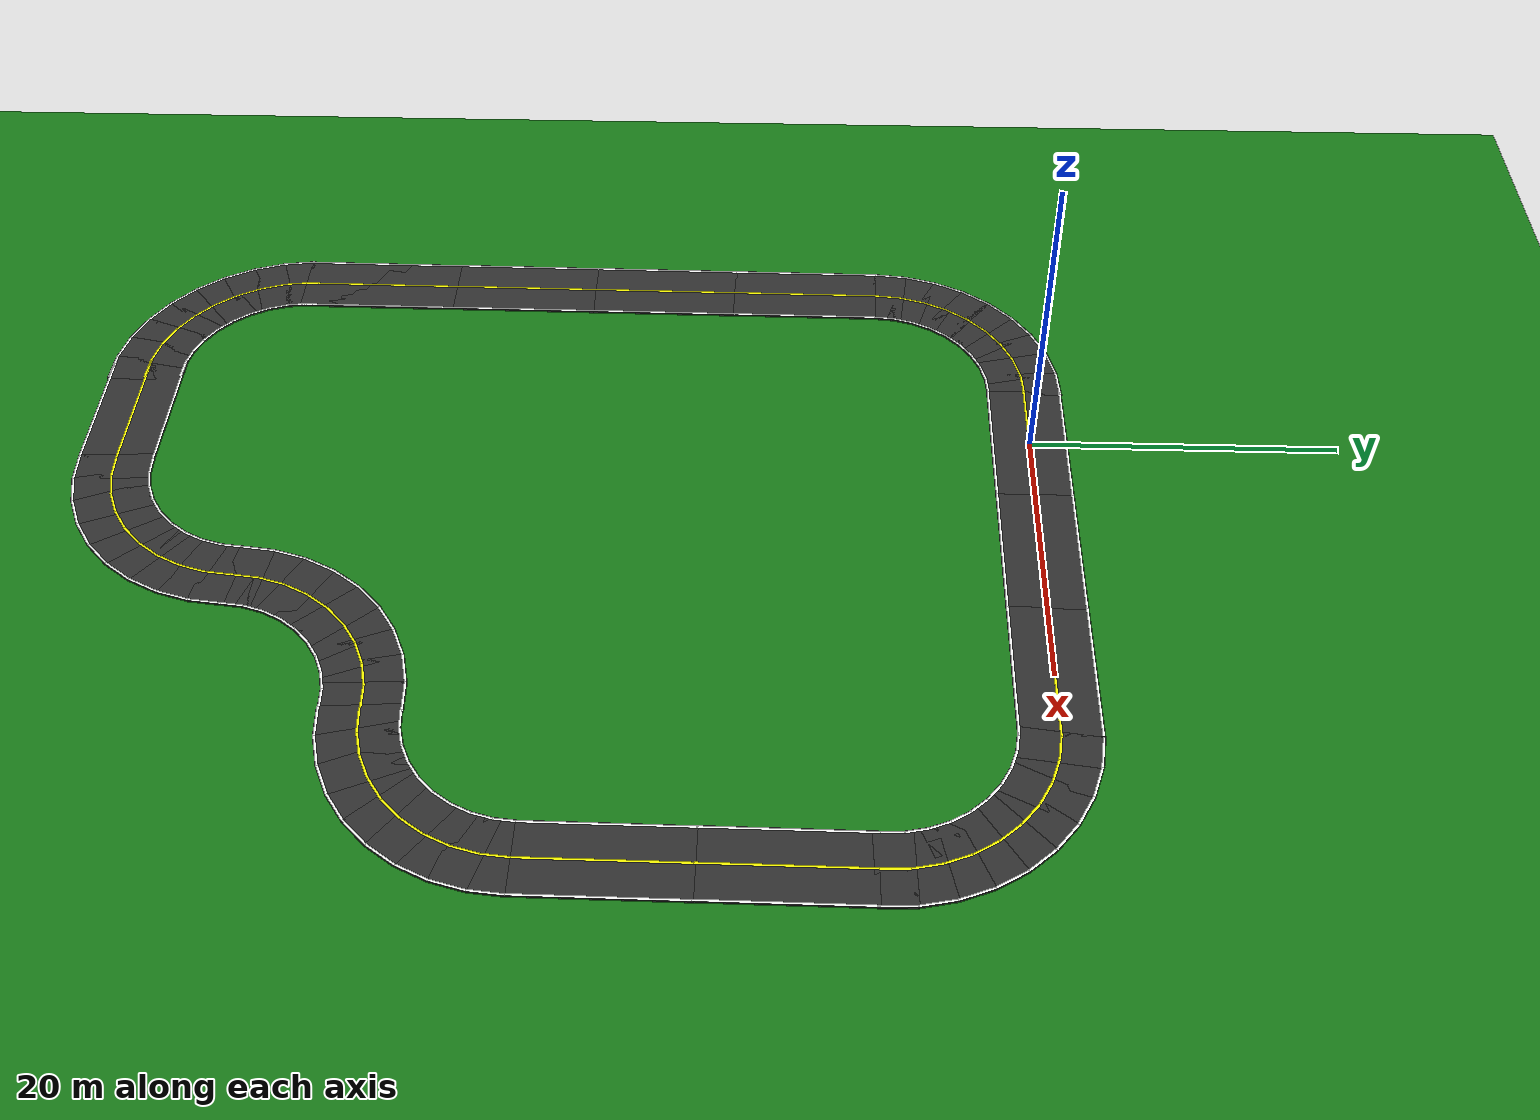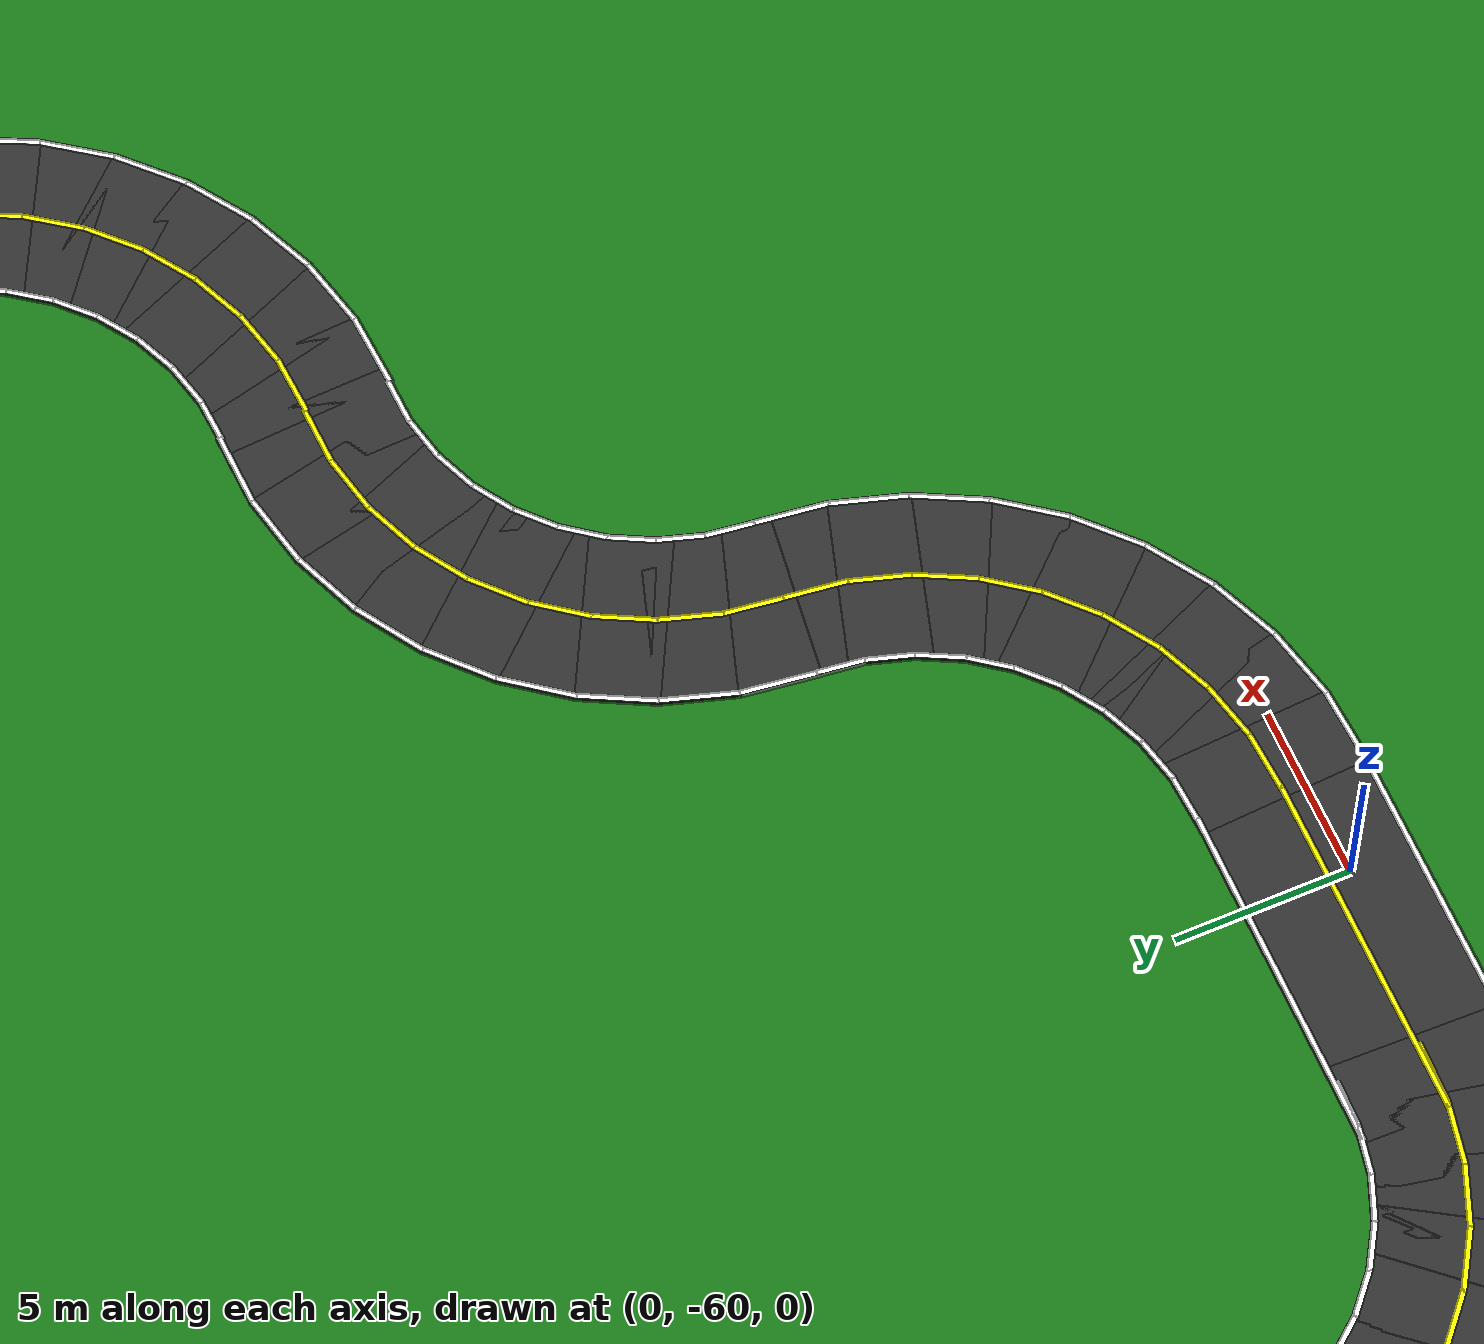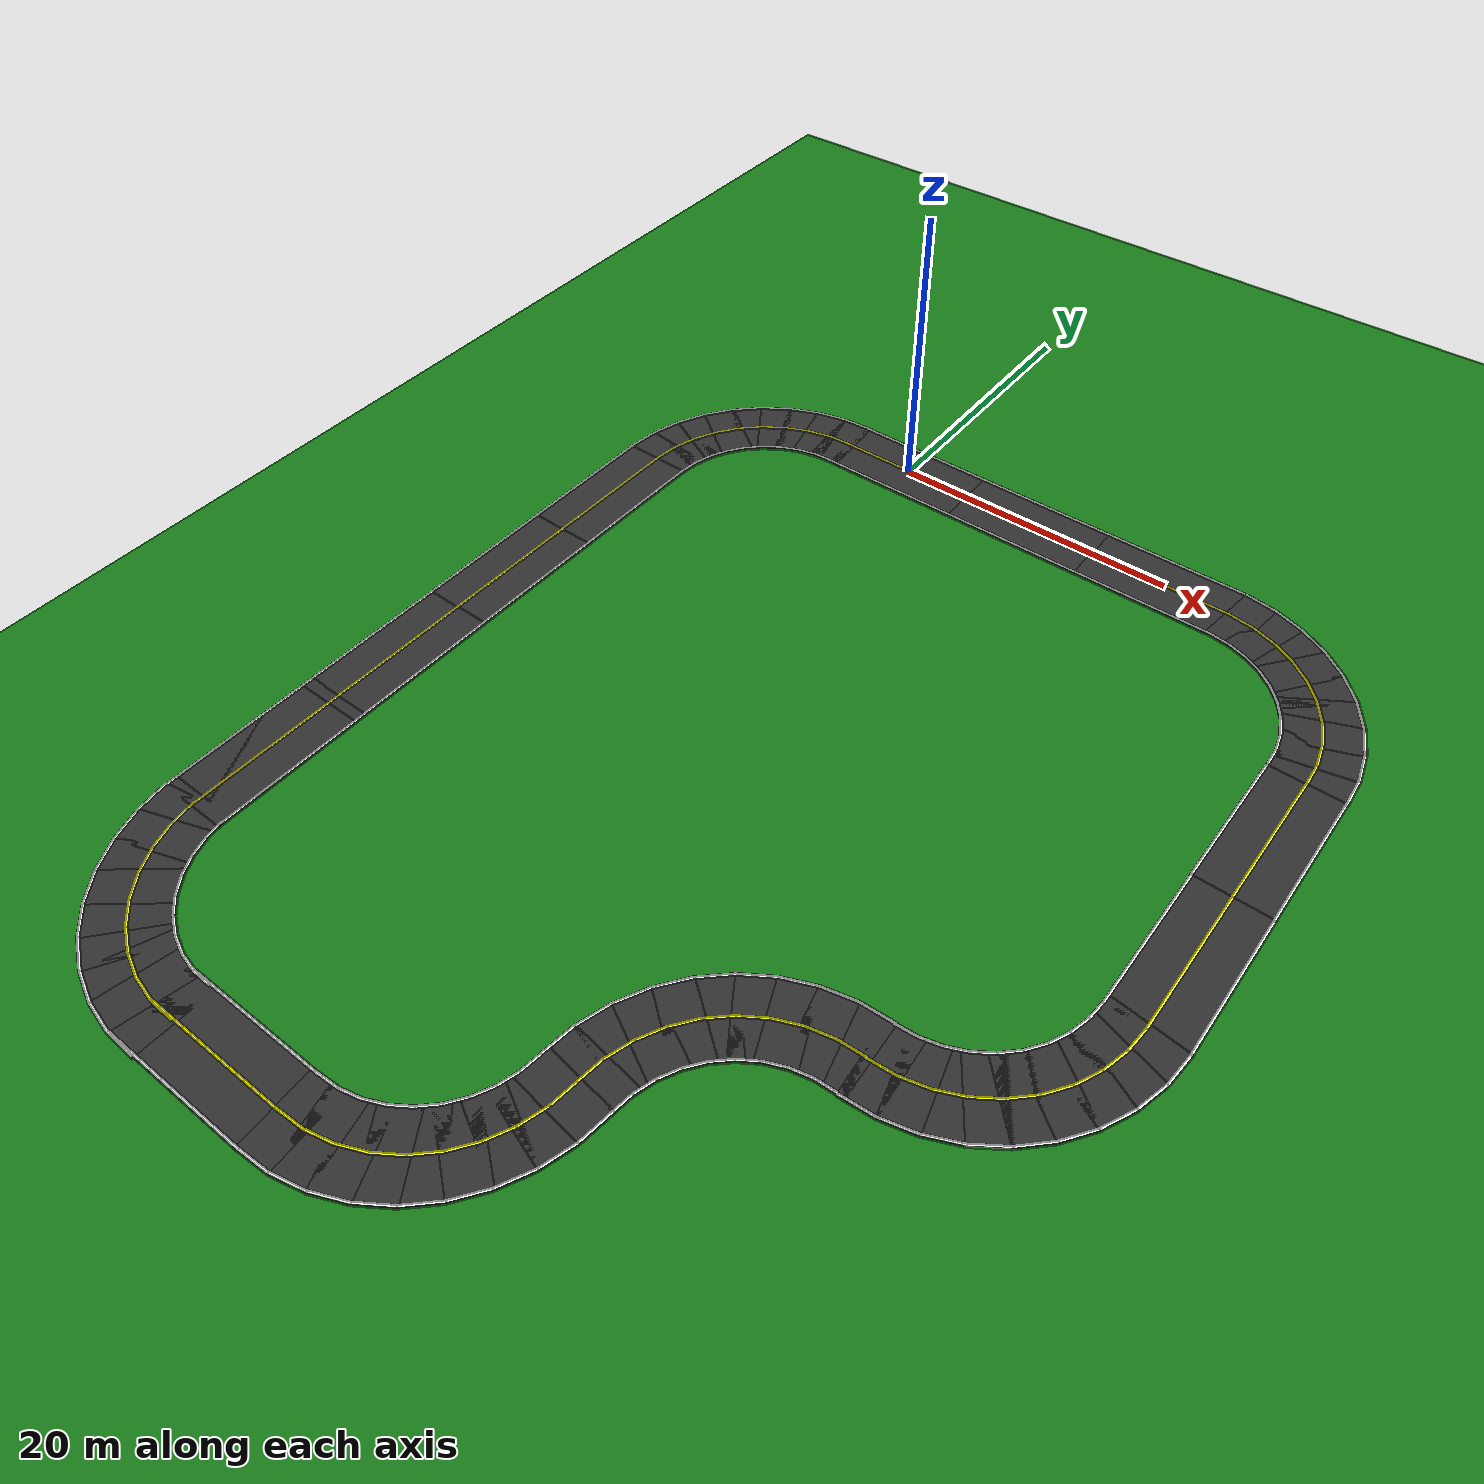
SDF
<sdf version="1.7">
 <world name="gas_station_3">
  <light name="sun" type="directional">
   <pose>0 0 10 0 -0 0</pose>
   <diffuse>0.8 0.8 0.8 1</diffuse>
   <specular>0.2 0.2 0.2 1</specular>
   <attenuation>
    <range>1000</range>
    <constant>0.9</constant>
    <linear>0.01</linear>
    <quadratic>0.001</quadratic>
   </attenuation>
   <direction>-0.5 0.1 -0.9</direction>
   <spot><inner_angle>0</inner_angle><outer_angle>0</outer_angle><falloff>0</falloff></spot>
  </light>
  <model name="ground_plane">
   <static>1</static>
   <link name="link">
    <collision name="collision">
     <geometry><plane><normal>0 0 1</normal><size>100 100</size></plane></geometry>
     <surface>
      <contact><collide_bitmask>65535</collide_bitmask></contact>
      <friction><ode><mu>100</mu><mu2>50</mu2></ode></friction>
     </surface>
    </collision>
    <visual name="visual">
     <geometry><plane><normal>0 0 1</normal><size>100 100</size></plane></geometry>
     <material>
      <ambient>0.1 0.5 0.1 1</ambient>
      <diffuse>0.1 0.5 0.1 1</diffuse>
      <specular>0.1 0.1 0.1 1</specular>
     </material>
    </visual>
   </link>
   <pose>-0 -20 0 0 -0 0</pose>
  </model>
  <physics name="4ms" type="ignored">
   <max_step_size>0.004</max_step_size>
   <real_time_factor>0.5</real_time_factor>
  </physics>
  <plugin filename="ignition-gazebo-physics-system" name="ignition::gazebo::systems::Physics"/>
  <plugin filename="ignition-gazebo-user-commands-system" name="ignition::gazebo::systems::UserCommands"/>
  <plugin filename="ignition-gazebo-scene-broadcaster-system" name="ignition::gazebo::systems::SceneBroadcaster"/>
  <plugin filename="ignition-gazebo-sensors-system" name="ignition::gazebo::systems::Sensors">
   <render_engine>ogre2</render_engine>
  </plugin>
  <plugin filename="ignition-gazebo-imu-system" name="ignition::gazebo::systems::Imu"/>
  <atmosphere type="adiabatic"/>
  <scene><ambient>0.4 0.4 0.4 1</ambient><background>0.7 0.7 0.7 1</background><shadows>1</shadows></scene>
  <audio><device>default</device></audio>
  <spherical_coordinates>
   <surface_model>EARTH_WGS84</surface_model>
   <latitude_deg>0</latitude_deg>
   <longitude_deg>0</longitude_deg>
   <elevation>0</elevation>
   <heading_deg>0</heading_deg>
  </spherical_coordinates>
  <model name="road_straight">
   <static>1</static>
   <link name="link">
    <collision name="collision"><geometry><box><size>10 5 0.1</size></box></geometry></collision>
    <visual name="visual_surface">
     <geometry><box><size>10 5 0.1</size></box></geometry>
     <material>
      <ambient>0.2 0.2 0.2 1</ambient>
      <diffuse>0.2 0.2 0.2 1</diffuse>
      <specular>0.1 0.1 0.1 1</specular>
     </material>
    </visual>
    <visual name="visual_center_line">
     <pose>0 0 0.051 0 -0 0</pose>
     <geometry><box><size>10 0.15 0.001</size></box></geometry>
     <material><ambient>1 1 0 1</ambient><diffuse>1 1 0 1</diffuse></material>
    </visual>
    <visual name="visual_left_line">
     <pose>0 2.4 0.051 0 -0 0</pose>
     <geometry><box><size>10 0.15 0.001</size></box></geometry>
     <material><ambient>1 1 1 1</ambient><diffuse>1 1 1 1</diffuse></material>
    </visual>
    <visual name="visual_right_line">
     <pose>0 -2.4 0.051 0 -0 0</pose>
     <geometry><box><size>10 0.15 0.001</size></box></geometry>
     <material><ambient>1 1 1 1</ambient><diffuse>1 1 1 1</diffuse></material>
    </visual>
   </link>
   <pose>-0.248347 0.000542 0 0 -0 0</pose>
  </model>
  <model name="road_straight_clone">
   <static>1</static>
   <link name="link">
    <collision name="collision"><geometry><box><size>10 5 0.1</size></box></geometry></collision>
    <visual name="visual_surface">
     <geometry><box><size>10 5 0.1</size></box></geometry>
     <material>
      <ambient>0.2 0.2 0.2 1</ambient>
      <diffuse>0.2 0.2 0.2 1</diffuse>
      <specular>0.1 0.1 0.1 1</specular>
     </material>
    </visual>
    <visual name="visual_center_line">
     <pose>0 0 0.051 0 -0 0</pose>
     <geometry><box><size>10 0.15 0.001</size></box></geometry>
     <material><ambient>1 1 0 1</ambient><diffuse>1 1 0 1</diffuse></material>
    </visual>
    <visual name="visual_left_line">
     <pose>0 2.4 0.051 0 -0 0</pose>
     <geometry><box><size>10 0.15 0.001</size></box></geometry>
     <material><ambient>1 1 1 1</ambient><diffuse>1 1 1 1</diffuse></material>
    </visual>
    <visual name="visual_right_line">
     <pose>0 -2.4 0.051 0 -0 0</pose>
     <geometry><box><size>10 0.15 0.001</size></box></geometry>
     <material><ambient>1 1 1 1</ambient><diffuse>1 1 1 1</diffuse></material>
    </visual>
   </link>
   <pose>9.70219 0.000539 0 0 -0 0</pose>
  </model>
  <model name="road_straight_clone_clone">
   <static>1</static>
   <link name="link">
    <collision name="collision"><geometry><box><size>10 5 0.1</size></box></geometry></collision>
    <visual name="visual_surface">
     <geometry><box><size>10 5 0.1</size></box></geometry>
     <material>
      <ambient>0.2 0.2 0.2 1</ambient>
      <diffuse>0.2 0.2 0.2 1</diffuse>
      <specular>0.1 0.1 0.1 1</specular>
     </material>
    </visual>
    <visual name="visual_center_line">
     <pose>0 0 0.051 0 -0 0</pose>
     <geometry><box><size>10 0.15 0.001</size></box></geometry>
     <material><ambient>1 1 0 1</ambient><diffuse>1 1 0 1</diffuse></material>
    </visual>
    <visual name="visual_left_line">
     <pose>0 2.4 0.051 0 -0 0</pose>
     <geometry><box><size>10 0.15 0.001</size></box></geometry>
     <material><ambient>1 1 1 1</ambient><diffuse>1 1 1 1</diffuse></material>
    </visual>
    <visual name="visual_right_line">
     <pose>0 -2.4 0.051 0 -0 0</pose>
     <geometry><box><size>10 0.15 0.001</size></box></geometry>
     <material><ambient>1 1 1 1</ambient><diffuse>1 1 1 1</diffuse></material>
    </visual>
   </link>
   <pose>19.59 0.00396 0 0 -0 0</pose>
  </model>
  <model name="road_curved">
   <static>1</static>
   <link name="link">
    <visual name="visual_segment_0">
     <pose>0.8716 0.0381 0 0 -0 0.0873</pose>
     <geometry><box><size>2.2789 5 0.1</size></box></geometry>
     <material>
      <ambient>0.2 0.2 0.2 1</ambient>
      <diffuse>0.2 0.2 0.2 1</diffuse>
      <specular>0.1 0.1 0.1 1</specular>
     </material>
    </visual>
    <collision name="collision_segment_0">
     <pose>0.8716 0.0381 0 0 -0 0.0873</pose>
     <geometry><box><size>2.2789 5 0.1</size></box></geometry>
    </collision>
    <visual name="visual_center_line_0">
     <pose>0.8716 0.0381 0.051 0 -0 0.0873</pose>
     <geometry><box><size>1.7931 0.15 0.001</size></box></geometry>
     <material><ambient>1 1 0 1</ambient><diffuse>1 1 0 1</diffuse></material>
    </visual>
    <visual name="visual_inner_line_0">
     <pose>0.6624 2.4289 0.051 0 -0 0.0873</pose>
     <geometry><box><size>1.3748 0.15 0.001</size></box></geometry>
     <material><ambient>1 1 1 1</ambient><diffuse>1 1 1 1</diffuse></material>
    </visual>
    <visual name="visual_outer_line_0">
     <pose>1.0807 -2.3528 0.051 0 -0 0.0873</pose>
     <geometry><box><size>2.2115 0.15 0.001</size></box></geometry>
     <material><ambient>1 1 1 1</ambient><diffuse>1 1 1 1</diffuse></material>
    </visual>
    <visual name="visual_segment_1">
     <pose>2.5882 0.3407 0 0 -0 0.2618</pose>
     <geometry><box><size>2.2789 5 0.1</size></box></geometry>
     <material>
      <ambient>0.2 0.2 0.2 1</ambient>
      <diffuse>0.2 0.2 0.2 1</diffuse>
      <specular>0.1 0.1 0.1 1</specular>
     </material>
    </visual>
    <collision name="collision_segment_1">
     <pose>2.5882 0.3407 0 0 -0 0.2618</pose>
     <geometry><box><size>2.2789 5 0.1</size></box></geometry>
    </collision>
    <visual name="visual_center_line_1">
     <pose>2.5882 0.3407 0.051 0 -0 0.2618</pose>
     <geometry><box><size>1.7931 0.15 0.001</size></box></geometry>
     <material><ambient>1 1 0 1</ambient><diffuse>1 1 0 1</diffuse></material>
    </visual>
    <visual name="visual_inner_line_1">
     <pose>1.967 2.659 0.051 0 -0 0.2618</pose>
     <geometry><box><size>1.3748 0.15 0.001</size></box></geometry>
     <material><ambient>1 1 1 1</ambient><diffuse>1 1 1 1</diffuse></material>
    </visual>
    <visual name="visual_outer_line_1">
     <pose>3.2094 -1.9775 0.051 0 -0 0.2618</pose>
     <geometry><box><size>2.2115 0.15 0.001</size></box></geometry>
     <material><ambient>1 1 1 1</ambient><diffuse>1 1 1 1</diffuse></material>
    </visual>
    <visual name="visual_segment_2">
     <pose>4.2262 0.9369 0 0 -0 0.4363</pose>
     <geometry><box><size>2.2789 5 0.1</size></box></geometry>
     <material>
      <ambient>0.2 0.2 0.2 1</ambient>
      <diffuse>0.2 0.2 0.2 1</diffuse>
      <specular>0.1 0.1 0.1 1</specular>
     </material>
    </visual>
    <collision name="collision_segment_2">
     <pose>4.2262 0.9369 0 0 -0 0.4363</pose>
     <geometry><box><size>2.2789 5 0.1</size></box></geometry>
    </collision>
    <visual name="visual_center_line_2">
     <pose>4.2262 0.9369 0.051 0 -0 0.4363</pose>
     <geometry><box><size>1.7931 0.15 0.001</size></box></geometry>
     <material><ambient>1 1 0 1</ambient><diffuse>1 1 0 1</diffuse></material>
    </visual>
    <visual name="visual_inner_line_2">
     <pose>3.2119 3.1121 0.051 0 -0 0.4363</pose>
     <geometry><box><size>1.3748 0.15 0.001</size></box></geometry>
     <material><ambient>1 1 1 1</ambient><diffuse>1 1 1 1</diffuse></material>
    </visual>
    <visual name="visual_outer_line_2">
     <pose>5.2405 -1.2382 0.051 0 -0 0.4363</pose>
     <geometry><box><size>2.2115 0.15 0.001</size></box></geometry>
     <material><ambient>1 1 1 1</ambient><diffuse>1 1 1 1</diffuse></material>
    </visual>
    <visual name="visual_segment_3">
     <pose>5.7358 1.8085 0 0 -0 0.6109</pose>
     <geometry><box><size>2.2789 5 0.1</size></box></geometry>
     <material>
      <ambient>0.2 0.2 0.2 1</ambient>
      <diffuse>0.2 0.2 0.2 1</diffuse>
      <specular>0.1 0.1 0.1 1</specular>
     </material>
    </visual>
    <collision name="collision_segment_3">
     <pose>5.7358 1.8085 0 0 -0 0.6109</pose>
     <geometry><box><size>2.2789 5 0.1</size></box></geometry>
    </collision>
    <visual name="visual_center_line_3">
     <pose>5.7358 1.8085 0.051 0 -0 0.6109</pose>
     <geometry><box><size>1.7931 0.15 0.001</size></box></geometry>
     <material><ambient>1 1 0 1</ambient><diffuse>1 1 0 1</diffuse></material>
    </visual>
    <visual name="visual_inner_line_3">
     <pose>4.3592 3.7744 0.051 0 -0 0.6109</pose>
     <geometry><box><size>1.3748 0.15 0.001</size></box></geometry>
     <material><ambient>1 1 1 1</ambient><diffuse>1 1 1 1</diffuse></material>
    </visual>
    <visual name="visual_outer_line_3">
     <pose>7.1123 -0.1575 0.051 0 -0 0.6109</pose>
     <geometry><box><size>2.2115 0.15 0.001</size></box></geometry>
     <material><ambient>1 1 1 1</ambient><diffuse>1 1 1 1</diffuse></material>
    </visual>
    <visual name="visual_segment_4">
     <pose>7.0711 2.9289 0 0 -0 0.7854</pose>
     <geometry><box><size>2.2789 5 0.1</size></box></geometry>
     <material>
      <ambient>0.2 0.2 0.2 1</ambient>
      <diffuse>0.2 0.2 0.2 1</diffuse>
      <specular>0.1 0.1 0.1 1</specular>
     </material>
    </visual>
    <collision name="collision_segment_4">
     <pose>7.0711 2.9289 0 0 -0 0.7854</pose>
     <geometry><box><size>2.2789 5 0.1</size></box></geometry>
    </collision>
    <visual name="visual_center_line_4">
     <pose>7.0711 2.9289 0.051 0 -0 0.7854</pose>
     <geometry><box><size>1.7931 0.15 0.001</size></box></geometry>
     <material><ambient>1 1 0 1</ambient><diffuse>1 1 0 1</diffuse></material>
    </visual>
    <visual name="visual_inner_line_4">
     <pose>5.374 4.626 0.051 0 -0 0.7854</pose>
     <geometry><box><size>1.3748 0.15 0.001</size></box></geometry>
     <material><ambient>1 1 1 1</ambient><diffuse>1 1 1 1</diffuse></material>
    </visual>
    <visual name="visual_outer_line_4">
     <pose>8.7681 1.2319 0.051 0 -0 0.7854</pose>
     <geometry><box><size>2.2115 0.15 0.001</size></box></geometry>
     <material><ambient>1 1 1 1</ambient><diffuse>1 1 1 1</diffuse></material>
    </visual>
    <visual name="visual_segment_5">
     <pose>8.1915 4.2642 0 0 -0 0.9599</pose>
     <geometry><box><size>2.2789 5 0.1</size></box></geometry>
     <material>
      <ambient>0.2 0.2 0.2 1</ambient>
      <diffuse>0.2 0.2 0.2 1</diffuse>
      <specular>0.1 0.1 0.1 1</specular>
     </material>
    </visual>
    <collision name="collision_segment_5">
     <pose>8.1915 4.2642 0 0 -0 0.9599</pose>
     <geometry><box><size>2.2789 5 0.1</size></box></geometry>
    </collision>
    <visual name="visual_center_line_5">
     <pose>8.1915 4.2642 0.051 0 -0 0.9599</pose>
     <geometry><box><size>1.7931 0.15 0.001</size></box></geometry>
     <material><ambient>1 1 0 1</ambient><diffuse>1 1 0 1</diffuse></material>
    </visual>
    <visual name="visual_inner_line_5">
     <pose>6.2256 5.6408 0.051 0 -0 0.9599</pose>
     <geometry><box><size>1.3748 0.15 0.001</size></box></geometry>
     <material><ambient>1 1 1 1</ambient><diffuse>1 1 1 1</diffuse></material>
    </visual>
    <visual name="visual_outer_line_5">
     <pose>10.1575 2.8877 0.051 0 -0 0.9599</pose>
     <geometry><box><size>2.2115 0.15 0.001</size></box></geometry>
     <material><ambient>1 1 1 1</ambient><diffuse>1 1 1 1</diffuse></material>
    </visual>
    <visual name="visual_segment_6">
     <pose>9.0631 5.7738 0 0 -0 1.1345</pose>
     <geometry><box><size>2.2789 5 0.1</size></box></geometry>
     <material>
      <ambient>0.2 0.2 0.2 1</ambient>
      <diffuse>0.2 0.2 0.2 1</diffuse>
      <specular>0.1 0.1 0.1 1</specular>
     </material>
    </visual>
    <collision name="collision_segment_6">
     <pose>9.0631 5.7738 0 0 -0 1.1345</pose>
     <geometry><box><size>2.2789 5 0.1</size></box></geometry>
    </collision>
    <visual name="visual_center_line_6">
     <pose>9.0631 5.7738 0.051 0 -0 1.1345</pose>
     <geometry><box><size>1.7931 0.15 0.001</size></box></geometry>
     <material><ambient>1 1 0 1</ambient><diffuse>1 1 0 1</diffuse></material>
    </visual>
    <visual name="visual_inner_line_6">
     <pose>6.8879 6.7881 0.051 0 -0 1.1345</pose>
     <geometry><box><size>1.3748 0.15 0.001</size></box></geometry>
     <material><ambient>1 1 1 1</ambient><diffuse>1 1 1 1</diffuse></material>
    </visual>
    <visual name="visual_outer_line_6">
     <pose>11.2382 4.7595 0.051 0 -0 1.1345</pose>
     <geometry><box><size>2.2115 0.15 0.001</size></box></geometry>
     <material><ambient>1 1 1 1</ambient><diffuse>1 1 1 1</diffuse></material>
    </visual>
    <visual name="visual_segment_7">
     <pose>9.6593 7.4118 0 0 -0 1.309</pose>
     <geometry><box><size>2.2789 5 0.1</size></box></geometry>
     <material>
      <ambient>0.2 0.2 0.2 1</ambient>
      <diffuse>0.2 0.2 0.2 1</diffuse>
      <specular>0.1 0.1 0.1 1</specular>
     </material>
    </visual>
    <collision name="collision_segment_7">
     <pose>9.6593 7.4118 0 0 -0 1.309</pose>
     <geometry><box><size>2.2789 5 0.1</size></box></geometry>
    </collision>
    <visual name="visual_center_line_7">
     <pose>9.6593 7.4118 0.051 0 -0 1.309</pose>
     <geometry><box><size>1.7931 0.15 0.001</size></box></geometry>
     <material><ambient>1 1 0 1</ambient><diffuse>1 1 0 1</diffuse></material>
    </visual>
    <visual name="visual_inner_line_7">
     <pose>7.341 8.033 0.051 0 -0 1.309</pose>
     <geometry><box><size>1.3748 0.15 0.001</size></box></geometry>
     <material><ambient>1 1 1 1</ambient><diffuse>1 1 1 1</diffuse></material>
    </visual>
    <visual name="visual_outer_line_7">
     <pose>11.9775 6.7906 0.051 0 -0 1.309</pose>
     <geometry><box><size>2.2115 0.15 0.001</size></box></geometry>
     <material><ambient>1 1 1 1</ambient><diffuse>1 1 1 1</diffuse></material>
    </visual>
    <visual name="visual_segment_8">
     <pose>9.9619 9.1284 0 0 -0 1.4835</pose>
     <geometry><box><size>2.2789 5 0.1</size></box></geometry>
     <material>
      <ambient>0.2 0.2 0.2 1</ambient>
      <diffuse>0.2 0.2 0.2 1</diffuse>
      <specular>0.1 0.1 0.1 1</specular>
     </material>
    </visual>
    <collision name="collision_segment_8">
     <pose>9.9619 9.1284 0 0 -0 1.4835</pose>
     <geometry><box><size>2.2789 5 0.1</size></box></geometry>
    </collision>
    <visual name="visual_center_line_8">
     <pose>9.9619 9.1284 0.051 0 -0 1.4835</pose>
     <geometry><box><size>1.7931 0.15 0.001</size></box></geometry>
     <material><ambient>1 1 0 1</ambient><diffuse>1 1 0 1</diffuse></material>
    </visual>
    <visual name="visual_inner_line_8">
     <pose>7.5711 9.3376 0.051 0 -0 1.4835</pose>
     <geometry><box><size>1.3748 0.15 0.001</size></box></geometry>
     <material><ambient>1 1 1 1</ambient><diffuse>1 1 1 1</diffuse></material>
    </visual>
    <visual name="visual_outer_line_8">
     <pose>12.3528 8.9193 0.051 0 -0 1.4835</pose>
     <geometry><box><size>2.2115 0.15 0.001</size></box></geometry>
     <material><ambient>1 1 1 1</ambient><diffuse>1 1 1 1</diffuse></material>
    </visual>
   </link>
   <pose>34.0263 -10.5358 0 0 -0 1.51926</pose>
  </model>
  <model name="road_straight_clone_clone_clone">
   <static>1</static>
   <link name="link">
    <collision name="collision"><geometry><box><size>10 5 0.1</size></box></geometry></collision>
    <visual name="visual_surface">
     <geometry><box><size>10 5 0.1</size></box></geometry>
     <material>
      <ambient>0.2 0.2 0.2 1</ambient>
      <diffuse>0.2 0.2 0.2 1</diffuse>
      <specular>0.1 0.1 0.1 1</specular>
     </material>
    </visual>
    <visual name="visual_center_line">
     <pose>0 0 0.051 0 -0 0</pose>
     <geometry><box><size>10 0.15 0.001</size></box></geometry>
     <material><ambient>1 1 0 1</ambient><diffuse>1 1 0 1</diffuse></material>
    </visual>
    <visual name="visual_left_line">
     <pose>0 2.4 0.051 0 -0 0</pose>
     <geometry><box><size>10 0.15 0.001</size></box></geometry>
     <material><ambient>1 1 1 1</ambient><diffuse>1 1 1 1</diffuse></material>
    </visual>
    <visual name="visual_right_line">
     <pose>0 -2.4 0.051 0 -0 0</pose>
     <geometry><box><size>10 0.15 0.001</size></box></geometry>
     <material><ambient>1 1 1 1</ambient><diffuse>1 1 1 1</diffuse></material>
    </visual>
   </link>
   <pose>33.9982 -15.4816 0 0 -0 1.56099</pose>
  </model>
  <model name="road_straight_clone_clone_clone_clone">
   <static>1</static>
   <link name="link">
    <collision name="collision"><geometry><box><size>10 5 0.1</size></box></geometry></collision>
    <visual name="visual_surface">
     <geometry><box><size>10 5 0.1</size></box></geometry>
     <material>
      <ambient>0.2 0.2 0.2 1</ambient>
      <diffuse>0.2 0.2 0.2 1</diffuse>
      <specular>0.1 0.1 0.1 1</specular>
     </material>
    </visual>
    <visual name="visual_center_line">
     <pose>0 0 0.051 0 -0 0</pose>
     <geometry><box><size>10 0.15 0.001</size></box></geometry>
     <material><ambient>1 1 0 1</ambient><diffuse>1 1 0 1</diffuse></material>
    </visual>
    <visual name="visual_left_line">
     <pose>0 2.4 0.051 0 -0 0</pose>
     <geometry><box><size>10 0.15 0.001</size></box></geometry>
     <material><ambient>1 1 1 1</ambient><diffuse>1 1 1 1</diffuse></material>
    </visual>
    <visual name="visual_right_line">
     <pose>0 -2.4 0.051 0 -0 0</pose>
     <geometry><box><size>10 0.15 0.001</size></box></geometry>
     <material><ambient>1 1 1 1</ambient><diffuse>1 1 1 1</diffuse></material>
    </visual>
   </link>
   <pose>33.9162 -25.3829 0 0 -0 1.56099</pose>
  </model>
  <model name="road_curved_clone">
   <static>1</static>
   <link name="link">
    <visual name="visual_segment_0">
     <pose>0.8716 0.0381 0 0 -0 0.0873</pose>
     <geometry><box><size>2.2789 5 0.1</size></box></geometry>
     <material>
      <ambient>0.2 0.2 0.2 1</ambient>
      <diffuse>0.2 0.2 0.2 1</diffuse>
      <specular>0.1 0.1 0.1 1</specular>
     </material>
    </visual>
    <collision name="collision_segment_0">
     <pose>0.8716 0.0381 0 0 -0 0.0873</pose>
     <geometry><box><size>2.2789 5 0.1</size></box></geometry>
    </collision>
    <visual name="visual_center_line_0">
     <pose>0.8716 0.0381 0.051 0 -0 0.0873</pose>
     <geometry><box><size>1.7931 0.15 0.001</size></box></geometry>
     <material><ambient>1 1 0 1</ambient><diffuse>1 1 0 1</diffuse></material>
    </visual>
    <visual name="visual_inner_line_0">
     <pose>0.6624 2.4289 0.051 0 -0 0.0873</pose>
     <geometry><box><size>1.3748 0.15 0.001</size></box></geometry>
     <material><ambient>1 1 1 1</ambient><diffuse>1 1 1 1</diffuse></material>
    </visual>
    <visual name="visual_outer_line_0">
     <pose>1.0807 -2.3528 0.051 0 -0 0.0873</pose>
     <geometry><box><size>2.2115 0.15 0.001</size></box></geometry>
     <material><ambient>1 1 1 1</ambient><diffuse>1 1 1 1</diffuse></material>
    </visual>
    <visual name="visual_segment_1">
     <pose>2.5882 0.3407 0 0 -0 0.2618</pose>
     <geometry><box><size>2.2789 5 0.1</size></box></geometry>
     <material>
      <ambient>0.2 0.2 0.2 1</ambient>
      <diffuse>0.2 0.2 0.2 1</diffuse>
      <specular>0.1 0.1 0.1 1</specular>
     </material>
    </visual>
    <collision name="collision_segment_1">
     <pose>2.5882 0.3407 0 0 -0 0.2618</pose>
     <geometry><box><size>2.2789 5 0.1</size></box></geometry>
    </collision>
    <visual name="visual_center_line_1">
     <pose>2.5882 0.3407 0.051 0 -0 0.2618</pose>
     <geometry><box><size>1.7931 0.15 0.001</size></box></geometry>
     <material><ambient>1 1 0 1</ambient><diffuse>1 1 0 1</diffuse></material>
    </visual>
    <visual name="visual_inner_line_1">
     <pose>1.967 2.659 0.051 0 -0 0.2618</pose>
     <geometry><box><size>1.3748 0.15 0.001</size></box></geometry>
     <material><ambient>1 1 1 1</ambient><diffuse>1 1 1 1</diffuse></material>
    </visual>
    <visual name="visual_outer_line_1">
     <pose>3.2094 -1.9775 0.051 0 -0 0.2618</pose>
     <geometry><box><size>2.2115 0.15 0.001</size></box></geometry>
     <material><ambient>1 1 1 1</ambient><diffuse>1 1 1 1</diffuse></material>
    </visual>
    <visual name="visual_segment_2">
     <pose>4.2262 0.9369 0 0 -0 0.4363</pose>
     <geometry><box><size>2.2789 5 0.1</size></box></geometry>
     <material>
      <ambient>0.2 0.2 0.2 1</ambient>
      <diffuse>0.2 0.2 0.2 1</diffuse>
      <specular>0.1 0.1 0.1 1</specular>
     </material>
    </visual>
    <collision name="collision_segment_2">
     <pose>4.2262 0.9369 0 0 -0 0.4363</pose>
     <geometry><box><size>2.2789 5 0.1</size></box></geometry>
    </collision>
    <visual name="visual_center_line_2">
     <pose>4.2262 0.9369 0.051 0 -0 0.4363</pose>
     <geometry><box><size>1.7931 0.15 0.001</size></box></geometry>
     <material><ambient>1 1 0 1</ambient><diffuse>1 1 0 1</diffuse></material>
    </visual>
    <visual name="visual_inner_line_2">
     <pose>3.2119 3.1121 0.051 0 -0 0.4363</pose>
     <geometry><box><size>1.3748 0.15 0.001</size></box></geometry>
     <material><ambient>1 1 1 1</ambient><diffuse>1 1 1 1</diffuse></material>
    </visual>
    <visual name="visual_outer_line_2">
     <pose>5.2405 -1.2382 0.051 0 -0 0.4363</pose>
     <geometry><box><size>2.2115 0.15 0.001</size></box></geometry>
     <material><ambient>1 1 1 1</ambient><diffuse>1 1 1 1</diffuse></material>
    </visual>
    <visual name="visual_segment_3">
     <pose>5.7358 1.8085 0 0 -0 0.6109</pose>
     <geometry><box><size>2.2789 5 0.1</size></box></geometry>
     <material>
      <ambient>0.2 0.2 0.2 1</ambient>
      <diffuse>0.2 0.2 0.2 1</diffuse>
      <specular>0.1 0.1 0.1 1</specular>
     </material>
    </visual>
    <collision name="collision_segment_3">
     <pose>5.7358 1.8085 0 0 -0 0.6109</pose>
     <geometry><box><size>2.2789 5 0.1</size></box></geometry>
    </collision>
    <visual name="visual_center_line_3">
     <pose>5.7358 1.8085 0.051 0 -0 0.6109</pose>
     <geometry><box><size>1.7931 0.15 0.001</size></box></geometry>
     <material><ambient>1 1 0 1</ambient><diffuse>1 1 0 1</diffuse></material>
    </visual>
    <visual name="visual_inner_line_3">
     <pose>4.3592 3.7744 0.051 0 -0 0.6109</pose>
     <geometry><box><size>1.3748 0.15 0.001</size></box></geometry>
     <material><ambient>1 1 1 1</ambient><diffuse>1 1 1 1</diffuse></material>
    </visual>
    <visual name="visual_outer_line_3">
     <pose>7.1123 -0.1575 0.051 0 -0 0.6109</pose>
     <geometry><box><size>2.2115 0.15 0.001</size></box></geometry>
     <material><ambient>1 1 1 1</ambient><diffuse>1 1 1 1</diffuse></material>
    </visual>
    <visual name="visual_segment_4">
     <pose>7.0711 2.9289 0 0 -0 0.7854</pose>
     <geometry><box><size>2.2789 5 0.1</size></box></geometry>
     <material>
      <ambient>0.2 0.2 0.2 1</ambient>
      <diffuse>0.2 0.2 0.2 1</diffuse>
      <specular>0.1 0.1 0.1 1</specular>
     </material>
    </visual>
    <collision name="collision_segment_4">
     <pose>7.0711 2.9289 0 0 -0 0.7854</pose>
     <geometry><box><size>2.2789 5 0.1</size></box></geometry>
    </collision>
    <visual name="visual_center_line_4">
     <pose>7.0711 2.9289 0.051 0 -0 0.7854</pose>
     <geometry><box><size>1.7931 0.15 0.001</size></box></geometry>
     <material><ambient>1 1 0 1</ambient><diffuse>1 1 0 1</diffuse></material>
    </visual>
    <visual name="visual_inner_line_4">
     <pose>5.374 4.626 0.051 0 -0 0.7854</pose>
     <geometry><box><size>1.3748 0.15 0.001</size></box></geometry>
     <material><ambient>1 1 1 1</ambient><diffuse>1 1 1 1</diffuse></material>
    </visual>
    <visual name="visual_outer_line_4">
     <pose>8.7681 1.2319 0.051 0 -0 0.7854</pose>
     <geometry><box><size>2.2115 0.15 0.001</size></box></geometry>
     <material><ambient>1 1 1 1</ambient><diffuse>1 1 1 1</diffuse></material>
    </visual>
    <visual name="visual_segment_5">
     <pose>8.1915 4.2642 0 0 -0 0.9599</pose>
     <geometry><box><size>2.2789 5 0.1</size></box></geometry>
     <material>
      <ambient>0.2 0.2 0.2 1</ambient>
      <diffuse>0.2 0.2 0.2 1</diffuse>
      <specular>0.1 0.1 0.1 1</specular>
     </material>
    </visual>
    <collision name="collision_segment_5">
     <pose>8.1915 4.2642 0 0 -0 0.9599</pose>
     <geometry><box><size>2.2789 5 0.1</size></box></geometry>
    </collision>
    <visual name="visual_center_line_5">
     <pose>8.1915 4.2642 0.051 0 -0 0.9599</pose>
     <geometry><box><size>1.7931 0.15 0.001</size></box></geometry>
     <material><ambient>1 1 0 1</ambient><diffuse>1 1 0 1</diffuse></material>
    </visual>
    <visual name="visual_inner_line_5">
     <pose>6.2256 5.6408 0.051 0 -0 0.9599</pose>
     <geometry><box><size>1.3748 0.15 0.001</size></box></geometry>
     <material><ambient>1 1 1 1</ambient><diffuse>1 1 1 1</diffuse></material>
    </visual>
    <visual name="visual_outer_line_5">
     <pose>10.1575 2.8877 0.051 0 -0 0.9599</pose>
     <geometry><box><size>2.2115 0.15 0.001</size></box></geometry>
     <material><ambient>1 1 1 1</ambient><diffuse>1 1 1 1</diffuse></material>
    </visual>
    <visual name="visual_segment_6">
     <pose>9.0631 5.7738 0 0 -0 1.1345</pose>
     <geometry><box><size>2.2789 5 0.1</size></box></geometry>
     <material>
      <ambient>0.2 0.2 0.2 1</ambient>
      <diffuse>0.2 0.2 0.2 1</diffuse>
      <specular>0.1 0.1 0.1 1</specular>
     </material>
    </visual>
    <collision name="collision_segment_6">
     <pose>9.0631 5.7738 0 0 -0 1.1345</pose>
     <geometry><box><size>2.2789 5 0.1</size></box></geometry>
    </collision>
    <visual name="visual_center_line_6">
     <pose>9.0631 5.7738 0.051 0 -0 1.1345</pose>
     <geometry><box><size>1.7931 0.15 0.001</size></box></geometry>
     <material><ambient>1 1 0 1</ambient><diffuse>1 1 0 1</diffuse></material>
    </visual>
    <visual name="visual_inner_line_6">
     <pose>6.8879 6.7881 0.051 0 -0 1.1345</pose>
     <geometry><box><size>1.3748 0.15 0.001</size></box></geometry>
     <material><ambient>1 1 1 1</ambient><diffuse>1 1 1 1</diffuse></material>
    </visual>
    <visual name="visual_outer_line_6">
     <pose>11.2382 4.7595 0.051 0 -0 1.1345</pose>
     <geometry><box><size>2.2115 0.15 0.001</size></box></geometry>
     <material><ambient>1 1 1 1</ambient><diffuse>1 1 1 1</diffuse></material>
    </visual>
    <visual name="visual_segment_7">
     <pose>9.6593 7.4118 0 0 -0 1.309</pose>
     <geometry><box><size>2.2789 5 0.1</size></box></geometry>
     <material>
      <ambient>0.2 0.2 0.2 1</ambient>
      <diffuse>0.2 0.2 0.2 1</diffuse>
      <specular>0.1 0.1 0.1 1</specular>
     </material>
    </visual>
    <collision name="collision_segment_7">
     <pose>9.6593 7.4118 0 0 -0 1.309</pose>
     <geometry><box><size>2.2789 5 0.1</size></box></geometry>
    </collision>
    <visual name="visual_center_line_7">
     <pose>9.6593 7.4118 0.051 0 -0 1.309</pose>
     <geometry><box><size>1.7931 0.15 0.001</size></box></geometry>
     <material><ambient>1 1 0 1</ambient><diffuse>1 1 0 1</diffuse></material>
    </visual>
    <visual name="visual_inner_line_7">
     <pose>7.341 8.033 0.051 0 -0 1.309</pose>
     <geometry><box><size>1.3748 0.15 0.001</size></box></geometry>
     <material><ambient>1 1 1 1</ambient><diffuse>1 1 1 1</diffuse></material>
    </visual>
    <visual name="visual_outer_line_7">
     <pose>11.9775 6.7906 0.051 0 -0 1.309</pose>
     <geometry><box><size>2.2115 0.15 0.001</size></box></geometry>
     <material><ambient>1 1 1 1</ambient><diffuse>1 1 1 1</diffuse></material>
    </visual>
    <visual name="visual_segment_8">
     <pose>9.9619 9.1284 0 0 -0 1.4835</pose>
     <geometry><box><size>2.2789 5 0.1</size></box></geometry>
     <material>
      <ambient>0.2 0.2 0.2 1</ambient>
      <diffuse>0.2 0.2 0.2 1</diffuse>
      <specular>0.1 0.1 0.1 1</specular>
     </material>
    </visual>
    <collision name="collision_segment_8">
     <pose>9.9619 9.1284 0 0 -0 1.4835</pose>
     <geometry><box><size>2.2789 5 0.1</size></box></geometry>
    </collision>
    <visual name="visual_center_line_8">
     <pose>9.9619 9.1284 0.051 0 -0 1.4835</pose>
     <geometry><box><size>1.7931 0.15 0.001</size></box></geometry>
     <material><ambient>1 1 0 1</ambient><diffuse>1 1 0 1</diffuse></material>
    </visual>
    <visual name="visual_inner_line_8">
     <pose>7.5711 9.3376 0.051 0 -0 1.4835</pose>
     <geometry><box><size>1.3748 0.15 0.001</size></box></geometry>
     <material><ambient>1 1 1 1</ambient><diffuse>1 1 1 1</diffuse></material>
    </visual>
    <visual name="visual_outer_line_8">
     <pose>12.3528 8.9193 0.051 0 -0 1.4835</pose>
     <geometry><box><size>2.2115 0.15 0.001</size></box></geometry>
     <material><ambient>1 1 1 1</ambient><diffuse>1 1 1 1</diffuse></material>
    </visual>
   </link>
   <pose>23.6605 -40.1311 0 0 0 -0.017705</pose>
  </model>
  <model name="road_curved_clone_0">
   <static>1</static>
   <link name="link">
    <visual name="visual_segment_0">
     <pose>0.8716 0.0381 0 0 -0 0.0873</pose>
     <geometry><box><size>2.2789 5 0.1</size></box></geometry>
     <material>
      <ambient>0.2 0.2 0.2 1</ambient>
      <diffuse>0.2 0.2 0.2 1</diffuse>
      <specular>0.1 0.1 0.1 1</specular>
     </material>
    </visual>
    <collision name="collision_segment_0">
     <pose>0.8716 0.0381 0 0 -0 0.0873</pose>
     <geometry><box><size>2.2789 5 0.1</size></box></geometry>
    </collision>
    <visual name="visual_center_line_0">
     <pose>0.8716 0.0381 0.051 0 -0 0.0873</pose>
     <geometry><box><size>1.7931 0.15 0.001</size></box></geometry>
     <material><ambient>1 1 0 1</ambient><diffuse>1 1 0 1</diffuse></material>
    </visual>
    <visual name="visual_inner_line_0">
     <pose>0.6624 2.4289 0.051 0 -0 0.0873</pose>
     <geometry><box><size>1.3748 0.15 0.001</size></box></geometry>
     <material><ambient>1 1 1 1</ambient><diffuse>1 1 1 1</diffuse></material>
    </visual>
    <visual name="visual_outer_line_0">
     <pose>1.0807 -2.3528 0.051 0 -0 0.0873</pose>
     <geometry><box><size>2.2115 0.15 0.001</size></box></geometry>
     <material><ambient>1 1 1 1</ambient><diffuse>1 1 1 1</diffuse></material>
    </visual>
    <visual name="visual_segment_1">
     <pose>2.5882 0.3407 0 0 -0 0.2618</pose>
     <geometry><box><size>2.2789 5 0.1</size></box></geometry>
     <material>
      <ambient>0.2 0.2 0.2 1</ambient>
      <diffuse>0.2 0.2 0.2 1</diffuse>
      <specular>0.1 0.1 0.1 1</specular>
     </material>
    </visual>
    <collision name="collision_segment_1">
     <pose>2.5882 0.3407 0 0 -0 0.2618</pose>
     <geometry><box><size>2.2789 5 0.1</size></box></geometry>
    </collision>
    <visual name="visual_center_line_1">
     <pose>2.5882 0.3407 0.051 0 -0 0.2618</pose>
     <geometry><box><size>1.7931 0.15 0.001</size></box></geometry>
     <material><ambient>1 1 0 1</ambient><diffuse>1 1 0 1</diffuse></material>
    </visual>
    <visual name="visual_inner_line_1">
     <pose>1.967 2.659 0.051 0 -0 0.2618</pose>
     <geometry><box><size>1.3748 0.15 0.001</size></box></geometry>
     <material><ambient>1 1 1 1</ambient><diffuse>1 1 1 1</diffuse></material>
    </visual>
    <visual name="visual_outer_line_1">
     <pose>3.2094 -1.9775 0.051 0 -0 0.2618</pose>
     <geometry><box><size>2.2115 0.15 0.001</size></box></geometry>
     <material><ambient>1 1 1 1</ambient><diffuse>1 1 1 1</diffuse></material>
    </visual>
    <visual name="visual_segment_2">
     <pose>4.2262 0.9369 0 0 -0 0.4363</pose>
     <geometry><box><size>2.2789 5 0.1</size></box></geometry>
     <material>
      <ambient>0.2 0.2 0.2 1</ambient>
      <diffuse>0.2 0.2 0.2 1</diffuse>
      <specular>0.1 0.1 0.1 1</specular>
     </material>
    </visual>
    <collision name="collision_segment_2">
     <pose>4.2262 0.9369 0 0 -0 0.4363</pose>
     <geometry><box><size>2.2789 5 0.1</size></box></geometry>
    </collision>
    <visual name="visual_center_line_2">
     <pose>4.2262 0.9369 0.051 0 -0 0.4363</pose>
     <geometry><box><size>1.7931 0.15 0.001</size></box></geometry>
     <material><ambient>1 1 0 1</ambient><diffuse>1 1 0 1</diffuse></material>
    </visual>
    <visual name="visual_inner_line_2">
     <pose>3.2119 3.1121 0.051 0 -0 0.4363</pose>
     <geometry><box><size>1.3748 0.15 0.001</size></box></geometry>
     <material><ambient>1 1 1 1</ambient><diffuse>1 1 1 1</diffuse></material>
    </visual>
    <visual name="visual_outer_line_2">
     <pose>5.2405 -1.2382 0.051 0 -0 0.4363</pose>
     <geometry><box><size>2.2115 0.15 0.001</size></box></geometry>
     <material><ambient>1 1 1 1</ambient><diffuse>1 1 1 1</diffuse></material>
    </visual>
    <visual name="visual_segment_3">
     <pose>5.7358 1.8085 0 0 -0 0.6109</pose>
     <geometry><box><size>2.2789 5 0.1</size></box></geometry>
     <material>
      <ambient>0.2 0.2 0.2 1</ambient>
      <diffuse>0.2 0.2 0.2 1</diffuse>
      <specular>0.1 0.1 0.1 1</specular>
     </material>
    </visual>
    <collision name="collision_segment_3">
     <pose>5.7358 1.8085 0 0 -0 0.6109</pose>
     <geometry><box><size>2.2789 5 0.1</size></box></geometry>
    </collision>
    <visual name="visual_center_line_3">
     <pose>5.7358 1.8085 0.051 0 -0 0.6109</pose>
     <geometry><box><size>1.7931 0.15 0.001</size></box></geometry>
     <material><ambient>1 1 0 1</ambient><diffuse>1 1 0 1</diffuse></material>
    </visual>
    <visual name="visual_inner_line_3">
     <pose>4.3592 3.7744 0.051 0 -0 0.6109</pose>
     <geometry><box><size>1.3748 0.15 0.001</size></box></geometry>
     <material><ambient>1 1 1 1</ambient><diffuse>1 1 1 1</diffuse></material>
    </visual>
    <visual name="visual_outer_line_3">
     <pose>7.1123 -0.1575 0.051 0 -0 0.6109</pose>
     <geometry><box><size>2.2115 0.15 0.001</size></box></geometry>
     <material><ambient>1 1 1 1</ambient><diffuse>1 1 1 1</diffuse></material>
    </visual>
    <visual name="visual_segment_4">
     <pose>7.0711 2.9289 0 0 -0 0.7854</pose>
     <geometry><box><size>2.2789 5 0.1</size></box></geometry>
     <material>
      <ambient>0.2 0.2 0.2 1</ambient>
      <diffuse>0.2 0.2 0.2 1</diffuse>
      <specular>0.1 0.1 0.1 1</specular>
     </material>
    </visual>
    <collision name="collision_segment_4">
     <pose>7.0711 2.9289 0 0 -0 0.7854</pose>
     <geometry><box><size>2.2789 5 0.1</size></box></geometry>
    </collision>
    <visual name="visual_center_line_4">
     <pose>7.0711 2.9289 0.051 0 -0 0.7854</pose>
     <geometry><box><size>1.7931 0.15 0.001</size></box></geometry>
     <material><ambient>1 1 0 1</ambient><diffuse>1 1 0 1</diffuse></material>
    </visual>
    <visual name="visual_inner_line_4">
     <pose>5.374 4.626 0.051 0 -0 0.7854</pose>
     <geometry><box><size>1.3748 0.15 0.001</size></box></geometry>
     <material><ambient>1 1 1 1</ambient><diffuse>1 1 1 1</diffuse></material>
    </visual>
    <visual name="visual_outer_line_4">
     <pose>8.7681 1.2319 0.051 0 -0 0.7854</pose>
     <geometry><box><size>2.2115 0.15 0.001</size></box></geometry>
     <material><ambient>1 1 1 1</ambient><diffuse>1 1 1 1</diffuse></material>
    </visual>
    <visual name="visual_segment_5">
     <pose>8.1915 4.2642 0 0 -0 0.9599</pose>
     <geometry><box><size>2.2789 5 0.1</size></box></geometry>
     <material>
      <ambient>0.2 0.2 0.2 1</ambient>
      <diffuse>0.2 0.2 0.2 1</diffuse>
      <specular>0.1 0.1 0.1 1</specular>
     </material>
    </visual>
    <collision name="collision_segment_5">
     <pose>8.1915 4.2642 0 0 -0 0.9599</pose>
     <geometry><box><size>2.2789 5 0.1</size></box></geometry>
    </collision>
    <visual name="visual_center_line_5">
     <pose>8.1915 4.2642 0.051 0 -0 0.9599</pose>
     <geometry><box><size>1.7931 0.15 0.001</size></box></geometry>
     <material><ambient>1 1 0 1</ambient><diffuse>1 1 0 1</diffuse></material>
    </visual>
    <visual name="visual_inner_line_5">
     <pose>6.2256 5.6408 0.051 0 -0 0.9599</pose>
     <geometry><box><size>1.3748 0.15 0.001</size></box></geometry>
     <material><ambient>1 1 1 1</ambient><diffuse>1 1 1 1</diffuse></material>
    </visual>
    <visual name="visual_outer_line_5">
     <pose>10.1575 2.8877 0.051 0 -0 0.9599</pose>
     <geometry><box><size>2.2115 0.15 0.001</size></box></geometry>
     <material><ambient>1 1 1 1</ambient><diffuse>1 1 1 1</diffuse></material>
    </visual>
    <visual name="visual_segment_6">
     <pose>9.0631 5.7738 0 0 -0 1.1345</pose>
     <geometry><box><size>2.2789 5 0.1</size></box></geometry>
     <material>
      <ambient>0.2 0.2 0.2 1</ambient>
      <diffuse>0.2 0.2 0.2 1</diffuse>
      <specular>0.1 0.1 0.1 1</specular>
     </material>
    </visual>
    <collision name="collision_segment_6">
     <pose>9.0631 5.7738 0 0 -0 1.1345</pose>
     <geometry><box><size>2.2789 5 0.1</size></box></geometry>
    </collision>
    <visual name="visual_center_line_6">
     <pose>9.0631 5.7738 0.051 0 -0 1.1345</pose>
     <geometry><box><size>1.7931 0.15 0.001</size></box></geometry>
     <material><ambient>1 1 0 1</ambient><diffuse>1 1 0 1</diffuse></material>
    </visual>
    <visual name="visual_inner_line_6">
     <pose>6.8879 6.7881 0.051 0 -0 1.1345</pose>
     <geometry><box><size>1.3748 0.15 0.001</size></box></geometry>
     <material><ambient>1 1 1 1</ambient><diffuse>1 1 1 1</diffuse></material>
    </visual>
    <visual name="visual_outer_line_6">
     <pose>11.2382 4.7595 0.051 0 -0 1.1345</pose>
     <geometry><box><size>2.2115 0.15 0.001</size></box></geometry>
     <material><ambient>1 1 1 1</ambient><diffuse>1 1 1 1</diffuse></material>
    </visual>
    <visual name="visual_segment_7">
     <pose>9.6593 7.4118 0 0 -0 1.309</pose>
     <geometry><box><size>2.2789 5 0.1</size></box></geometry>
     <material>
      <ambient>0.2 0.2 0.2 1</ambient>
      <diffuse>0.2 0.2 0.2 1</diffuse>
      <specular>0.1 0.1 0.1 1</specular>
     </material>
    </visual>
    <collision name="collision_segment_7">
     <pose>9.6593 7.4118 0 0 -0 1.309</pose>
     <geometry><box><size>2.2789 5 0.1</size></box></geometry>
    </collision>
    <visual name="visual_center_line_7">
     <pose>9.6593 7.4118 0.051 0 -0 1.309</pose>
     <geometry><box><size>1.7931 0.15 0.001</size></box></geometry>
     <material><ambient>1 1 0 1</ambient><diffuse>1 1 0 1</diffuse></material>
    </visual>
    <visual name="visual_inner_line_7">
     <pose>7.341 8.033 0.051 0 -0 1.309</pose>
     <geometry><box><size>1.3748 0.15 0.001</size></box></geometry>
     <material><ambient>1 1 1 1</ambient><diffuse>1 1 1 1</diffuse></material>
    </visual>
    <visual name="visual_outer_line_7">
     <pose>11.9775 6.7906 0.051 0 -0 1.309</pose>
     <geometry><box><size>2.2115 0.15 0.001</size></box></geometry>
     <material><ambient>1 1 1 1</ambient><diffuse>1 1 1 1</diffuse></material>
    </visual>
    <visual name="visual_segment_8">
     <pose>9.9619 9.1284 0 0 -0 1.4835</pose>
     <geometry><box><size>2.2789 5 0.1</size></box></geometry>
     <material>
      <ambient>0.2 0.2 0.2 1</ambient>
      <diffuse>0.2 0.2 0.2 1</diffuse>
      <specular>0.1 0.1 0.1 1</specular>
     </material>
    </visual>
    <collision name="collision_segment_8">
     <pose>9.9619 9.1284 0 0 -0 1.4835</pose>
     <geometry><box><size>2.2789 5 0.1</size></box></geometry>
    </collision>
    <visual name="visual_center_line_8">
     <pose>9.9619 9.1284 0.051 0 -0 1.4835</pose>
     <geometry><box><size>1.7931 0.15 0.001</size></box></geometry>
     <material><ambient>1 1 0 1</ambient><diffuse>1 1 0 1</diffuse></material>
    </visual>
    <visual name="visual_inner_line_8">
     <pose>7.5711 9.3376 0.051 0 -0 1.4835</pose>
     <geometry><box><size>1.3748 0.15 0.001</size></box></geometry>
     <material><ambient>1 1 1 1</ambient><diffuse>1 1 1 1</diffuse></material>
    </visual>
    <visual name="visual_outer_line_8">
     <pose>12.3528 8.9193 0.051 0 -0 1.4835</pose>
     <geometry><box><size>2.2115 0.15 0.001</size></box></geometry>
     <material><ambient>1 1 1 1</ambient><diffuse>1 1 1 1</diffuse></material>
    </visual>
   </link>
   <pose>23.6842 -40.1646 0 0 -0 3.10157</pose>
  </model>
  <model name="road_curved_clone_0_clone">
   <static>1</static>
   <link name="link">
    <visual name="visual_segment_0">
     <pose>0.8716 0.0381 0 0 -0 0.0873</pose>
     <geometry><box><size>2.2789 5 0.1</size></box></geometry>
     <material>
      <ambient>0.2 0.2 0.2 1</ambient>
      <diffuse>0.2 0.2 0.2 1</diffuse>
      <specular>0.1 0.1 0.1 1</specular>
     </material>
    </visual>
    <collision name="collision_segment_0">
     <pose>0.8716 0.0381 0 0 -0 0.0873</pose>
     <geometry><box><size>2.2789 5 0.1</size></box></geometry>
    </collision>
    <visual name="visual_center_line_0">
     <pose>0.8716 0.0381 0.051 0 -0 0.0873</pose>
     <geometry><box><size>1.7931 0.15 0.001</size></box></geometry>
     <material><ambient>1 1 0 1</ambient><diffuse>1 1 0 1</diffuse></material>
    </visual>
    <visual name="visual_inner_line_0">
     <pose>0.6624 2.4289 0.051 0 -0 0.0873</pose>
     <geometry><box><size>1.3748 0.15 0.001</size></box></geometry>
     <material><ambient>1 1 1 1</ambient><diffuse>1 1 1 1</diffuse></material>
    </visual>
    <visual name="visual_outer_line_0">
     <pose>1.0807 -2.3528 0.051 0 -0 0.0873</pose>
     <geometry><box><size>2.2115 0.15 0.001</size></box></geometry>
     <material><ambient>1 1 1 1</ambient><diffuse>1 1 1 1</diffuse></material>
    </visual>
    <visual name="visual_segment_1">
     <pose>2.5882 0.3407 0 0 -0 0.2618</pose>
     <geometry><box><size>2.2789 5 0.1</size></box></geometry>
     <material>
      <ambient>0.2 0.2 0.2 1</ambient>
      <diffuse>0.2 0.2 0.2 1</diffuse>
      <specular>0.1 0.1 0.1 1</specular>
     </material>
    </visual>
    <collision name="collision_segment_1">
     <pose>2.5882 0.3407 0 0 -0 0.2618</pose>
     <geometry><box><size>2.2789 5 0.1</size></box></geometry>
    </collision>
    <visual name="visual_center_line_1">
     <pose>2.5882 0.3407 0.051 0 -0 0.2618</pose>
     <geometry><box><size>1.7931 0.15 0.001</size></box></geometry>
     <material><ambient>1 1 0 1</ambient><diffuse>1 1 0 1</diffuse></material>
    </visual>
    <visual name="visual_inner_line_1">
     <pose>1.967 2.659 0.051 0 -0 0.2618</pose>
     <geometry><box><size>1.3748 0.15 0.001</size></box></geometry>
     <material><ambient>1 1 1 1</ambient><diffuse>1 1 1 1</diffuse></material>
    </visual>
    <visual name="visual_outer_line_1">
     <pose>3.2094 -1.9775 0.051 0 -0 0.2618</pose>
     <geometry><box><size>2.2115 0.15 0.001</size></box></geometry>
     <material><ambient>1 1 1 1</ambient><diffuse>1 1 1 1</diffuse></material>
    </visual>
    <visual name="visual_segment_2">
     <pose>4.2262 0.9369 0 0 -0 0.4363</pose>
     <geometry><box><size>2.2789 5 0.1</size></box></geometry>
     <material>
      <ambient>0.2 0.2 0.2 1</ambient>
      <diffuse>0.2 0.2 0.2 1</diffuse>
      <specular>0.1 0.1 0.1 1</specular>
     </material>
    </visual>
    <collision name="collision_segment_2">
     <pose>4.2262 0.9369 0 0 -0 0.4363</pose>
     <geometry><box><size>2.2789 5 0.1</size></box></geometry>
    </collision>
    <visual name="visual_center_line_2">
     <pose>4.2262 0.9369 0.051 0 -0 0.4363</pose>
     <geometry><box><size>1.7931 0.15 0.001</size></box></geometry>
     <material><ambient>1 1 0 1</ambient><diffuse>1 1 0 1</diffuse></material>
    </visual>
    <visual name="visual_inner_line_2">
     <pose>3.2119 3.1121 0.051 0 -0 0.4363</pose>
     <geometry><box><size>1.3748 0.15 0.001</size></box></geometry>
     <material><ambient>1 1 1 1</ambient><diffuse>1 1 1 1</diffuse></material>
    </visual>
    <visual name="visual_outer_line_2">
     <pose>5.2405 -1.2382 0.051 0 -0 0.4363</pose>
     <geometry><box><size>2.2115 0.15 0.001</size></box></geometry>
     <material><ambient>1 1 1 1</ambient><diffuse>1 1 1 1</diffuse></material>
    </visual>
    <visual name="visual_segment_3">
     <pose>5.7358 1.8085 0 0 -0 0.6109</pose>
     <geometry><box><size>2.2789 5 0.1</size></box></geometry>
     <material>
      <ambient>0.2 0.2 0.2 1</ambient>
      <diffuse>0.2 0.2 0.2 1</diffuse>
      <specular>0.1 0.1 0.1 1</specular>
     </material>
    </visual>
    <collision name="collision_segment_3">
     <pose>5.7358 1.8085 0 0 -0 0.6109</pose>
     <geometry><box><size>2.2789 5 0.1</size></box></geometry>
    </collision>
    <visual name="visual_center_line_3">
     <pose>5.7358 1.8085 0.051 0 -0 0.6109</pose>
     <geometry><box><size>1.7931 0.15 0.001</size></box></geometry>
     <material><ambient>1 1 0 1</ambient><diffuse>1 1 0 1</diffuse></material>
    </visual>
    <visual name="visual_inner_line_3">
     <pose>4.3592 3.7744 0.051 0 -0 0.6109</pose>
     <geometry><box><size>1.3748 0.15 0.001</size></box></geometry>
     <material><ambient>1 1 1 1</ambient><diffuse>1 1 1 1</diffuse></material>
    </visual>
    <visual name="visual_outer_line_3">
     <pose>7.1123 -0.1575 0.051 0 -0 0.6109</pose>
     <geometry><box><size>2.2115 0.15 0.001</size></box></geometry>
     <material><ambient>1 1 1 1</ambient><diffuse>1 1 1 1</diffuse></material>
    </visual>
    <visual name="visual_segment_4">
     <pose>7.0711 2.9289 0 0 -0 0.7854</pose>
     <geometry><box><size>2.2789 5 0.1</size></box></geometry>
     <material>
      <ambient>0.2 0.2 0.2 1</ambient>
      <diffuse>0.2 0.2 0.2 1</diffuse>
      <specular>0.1 0.1 0.1 1</specular>
     </material>
    </visual>
    <collision name="collision_segment_4">
     <pose>7.0711 2.9289 0 0 -0 0.7854</pose>
     <geometry><box><size>2.2789 5 0.1</size></box></geometry>
    </collision>
    <visual name="visual_center_line_4">
     <pose>7.0711 2.9289 0.051 0 -0 0.7854</pose>
     <geometry><box><size>1.7931 0.15 0.001</size></box></geometry>
     <material><ambient>1 1 0 1</ambient><diffuse>1 1 0 1</diffuse></material>
    </visual>
    <visual name="visual_inner_line_4">
     <pose>5.374 4.626 0.051 0 -0 0.7854</pose>
     <geometry><box><size>1.3748 0.15 0.001</size></box></geometry>
     <material><ambient>1 1 1 1</ambient><diffuse>1 1 1 1</diffuse></material>
    </visual>
    <visual name="visual_outer_line_4">
     <pose>8.7681 1.2319 0.051 0 -0 0.7854</pose>
     <geometry><box><size>2.2115 0.15 0.001</size></box></geometry>
     <material><ambient>1 1 1 1</ambient><diffuse>1 1 1 1</diffuse></material>
    </visual>
    <visual name="visual_segment_5">
     <pose>8.1915 4.2642 0 0 -0 0.9599</pose>
     <geometry><box><size>2.2789 5 0.1</size></box></geometry>
     <material>
      <ambient>0.2 0.2 0.2 1</ambient>
      <diffuse>0.2 0.2 0.2 1</diffuse>
      <specular>0.1 0.1 0.1 1</specular>
     </material>
    </visual>
    <collision name="collision_segment_5">
     <pose>8.1915 4.2642 0 0 -0 0.9599</pose>
     <geometry><box><size>2.2789 5 0.1</size></box></geometry>
    </collision>
    <visual name="visual_center_line_5">
     <pose>8.1915 4.2642 0.051 0 -0 0.9599</pose>
     <geometry><box><size>1.7931 0.15 0.001</size></box></geometry>
     <material><ambient>1 1 0 1</ambient><diffuse>1 1 0 1</diffuse></material>
    </visual>
    <visual name="visual_inner_line_5">
     <pose>6.2256 5.6408 0.051 0 -0 0.9599</pose>
     <geometry><box><size>1.3748 0.15 0.001</size></box></geometry>
     <material><ambient>1 1 1 1</ambient><diffuse>1 1 1 1</diffuse></material>
    </visual>
    <visual name="visual_outer_line_5">
     <pose>10.1575 2.8877 0.051 0 -0 0.9599</pose>
     <geometry><box><size>2.2115 0.15 0.001</size></box></geometry>
     <material><ambient>1 1 1 1</ambient><diffuse>1 1 1 1</diffuse></material>
    </visual>
    <visual name="visual_segment_6">
     <pose>9.0631 5.7738 0 0 -0 1.1345</pose>
     <geometry><box><size>2.2789 5 0.1</size></box></geometry>
     <material>
      <ambient>0.2 0.2 0.2 1</ambient>
      <diffuse>0.2 0.2 0.2 1</diffuse>
      <specular>0.1 0.1 0.1 1</specular>
     </material>
    </visual>
    <collision name="collision_segment_6">
     <pose>9.0631 5.7738 0 0 -0 1.1345</pose>
     <geometry><box><size>2.2789 5 0.1</size></box></geometry>
    </collision>
    <visual name="visual_center_line_6">
     <pose>9.0631 5.7738 0.051 0 -0 1.1345</pose>
     <geometry><box><size>1.7931 0.15 0.001</size></box></geometry>
     <material><ambient>1 1 0 1</ambient><diffuse>1 1 0 1</diffuse></material>
    </visual>
    <visual name="visual_inner_line_6">
     <pose>6.8879 6.7881 0.051 0 -0 1.1345</pose>
     <geometry><box><size>1.3748 0.15 0.001</size></box></geometry>
     <material><ambient>1 1 1 1</ambient><diffuse>1 1 1 1</diffuse></material>
    </visual>
    <visual name="visual_outer_line_6">
     <pose>11.2382 4.7595 0.051 0 -0 1.1345</pose>
     <geometry><box><size>2.2115 0.15 0.001</size></box></geometry>
     <material><ambient>1 1 1 1</ambient><diffuse>1 1 1 1</diffuse></material>
    </visual>
    <visual name="visual_segment_7">
     <pose>9.6593 7.4118 0 0 -0 1.309</pose>
     <geometry><box><size>2.2789 5 0.1</size></box></geometry>
     <material>
      <ambient>0.2 0.2 0.2 1</ambient>
      <diffuse>0.2 0.2 0.2 1</diffuse>
      <specular>0.1 0.1 0.1 1</specular>
     </material>
    </visual>
    <collision name="collision_segment_7">
     <pose>9.6593 7.4118 0 0 -0 1.309</pose>
     <geometry><box><size>2.2789 5 0.1</size></box></geometry>
    </collision>
    <visual name="visual_center_line_7">
     <pose>9.6593 7.4118 0.051 0 -0 1.309</pose>
     <geometry><box><size>1.7931 0.15 0.001</size></box></geometry>
     <material><ambient>1 1 0 1</ambient><diffuse>1 1 0 1</diffuse></material>
    </visual>
    <visual name="visual_inner_line_7">
     <pose>7.341 8.033 0.051 0 -0 1.309</pose>
     <geometry><box><size>1.3748 0.15 0.001</size></box></geometry>
     <material><ambient>1 1 1 1</ambient><diffuse>1 1 1 1</diffuse></material>
    </visual>
    <visual name="visual_outer_line_7">
     <pose>11.9775 6.7906 0.051 0 -0 1.309</pose>
     <geometry><box><size>2.2115 0.15 0.001</size></box></geometry>
     <material><ambient>1 1 1 1</ambient><diffuse>1 1 1 1</diffuse></material>
    </visual>
    <visual name="visual_segment_8">
     <pose>9.9619 9.1284 0 0 -0 1.4835</pose>
     <geometry><box><size>2.2789 5 0.1</size></box></geometry>
     <material>
      <ambient>0.2 0.2 0.2 1</ambient>
      <diffuse>0.2 0.2 0.2 1</diffuse>
      <specular>0.1 0.1 0.1 1</specular>
     </material>
    </visual>
    <collision name="collision_segment_8">
     <pose>9.9619 9.1284 0 0 -0 1.4835</pose>
     <geometry><box><size>2.2789 5 0.1</size></box></geometry>
    </collision>
    <visual name="visual_center_line_8">
     <pose>9.9619 9.1284 0.051 0 -0 1.4835</pose>
     <geometry><box><size>1.7931 0.15 0.001</size></box></geometry>
     <material><ambient>1 1 0 1</ambient><diffuse>1 1 0 1</diffuse></material>
    </visual>
    <visual name="visual_inner_line_8">
     <pose>7.5711 9.3376 0.051 0 -0 1.4835</pose>
     <geometry><box><size>1.3748 0.15 0.001</size></box></geometry>
     <material><ambient>1 1 1 1</ambient><diffuse>1 1 1 1</diffuse></material>
    </visual>
    <visual name="visual_outer_line_8">
     <pose>12.3528 8.9193 0.051 0 -0 1.4835</pose>
     <geometry><box><size>2.2115 0.15 0.001</size></box></geometry>
     <material><ambient>1 1 1 1</ambient><diffuse>1 1 1 1</diffuse></material>
    </visual>
   </link>
   <pose>2.8952 -59.3495 0 0 0 -0.034162</pose>
  </model>
  <model name="road_straight_clone_clone_clone_0">
   <static>1</static>
   <link name="link">
    <collision name="collision"><geometry><box><size>10 5 0.1</size></box></geometry></collision>
    <visual name="visual_surface">
     <geometry><box><size>10 5 0.1</size></box></geometry>
     <material>
      <ambient>0.2 0.2 0.2 1</ambient>
      <diffuse>0.2 0.2 0.2 1</diffuse>
      <specular>0.1 0.1 0.1 1</specular>
     </material>
    </visual>
    <visual name="visual_center_line">
     <pose>0 0 0.051 0 -0 0</pose>
     <geometry><box><size>10 0.15 0.001</size></box></geometry>
     <material><ambient>1 1 0 1</ambient><diffuse>1 1 0 1</diffuse></material>
    </visual>
    <visual name="visual_left_line">
     <pose>0 2.4 0.051 0 -0 0</pose>
     <geometry><box><size>10 0.15 0.001</size></box></geometry>
     <material><ambient>1 1 1 1</ambient><diffuse>1 1 1 1</diffuse></material>
    </visual>
    <visual name="visual_right_line">
     <pose>0 -2.4 0.051 0 -0 0</pose>
     <geometry><box><size>10 0.15 0.001</size></box></geometry>
     <material><ambient>1 1 1 1</ambient><diffuse>1 1 1 1</diffuse></material>
    </visual>
   </link>
   <pose>-2.02069 -59.3978 0 0 -0 0</pose>
  </model>
  <model name="road_curved_clone_1">
   <static>1</static>
   <link name="link">
    <visual name="visual_segment_0">
     <pose>0.8716 0.0381 0 0 -0 0.0873</pose>
     <geometry><box><size>2.2789 5 0.1</size></box></geometry>
     <material>
      <ambient>0.2 0.2 0.2 1</ambient>
      <diffuse>0.2 0.2 0.2 1</diffuse>
      <specular>0.1 0.1 0.1 1</specular>
     </material>
    </visual>
    <collision name="collision_segment_0">
     <pose>0.8716 0.0381 0 0 -0 0.0873</pose>
     <geometry><box><size>2.2789 5 0.1</size></box></geometry>
    </collision>
    <visual name="visual_center_line_0">
     <pose>0.8716 0.0381 0.051 0 -0 0.0873</pose>
     <geometry><box><size>1.7931 0.15 0.001</size></box></geometry>
     <material><ambient>1 1 0 1</ambient><diffuse>1 1 0 1</diffuse></material>
    </visual>
    <visual name="visual_inner_line_0">
     <pose>0.6624 2.4289 0.051 0 -0 0.0873</pose>
     <geometry><box><size>1.3748 0.15 0.001</size></box></geometry>
     <material><ambient>1 1 1 1</ambient><diffuse>1 1 1 1</diffuse></material>
    </visual>
    <visual name="visual_outer_line_0">
     <pose>1.0807 -2.3528 0.051 0 -0 0.0873</pose>
     <geometry><box><size>2.2115 0.15 0.001</size></box></geometry>
     <material><ambient>1 1 1 1</ambient><diffuse>1 1 1 1</diffuse></material>
    </visual>
    <visual name="visual_segment_1">
     <pose>2.5882 0.3407 0 0 -0 0.2618</pose>
     <geometry><box><size>2.2789 5 0.1</size></box></geometry>
     <material>
      <ambient>0.2 0.2 0.2 1</ambient>
      <diffuse>0.2 0.2 0.2 1</diffuse>
      <specular>0.1 0.1 0.1 1</specular>
     </material>
    </visual>
    <collision name="collision_segment_1">
     <pose>2.5882 0.3407 0 0 -0 0.2618</pose>
     <geometry><box><size>2.2789 5 0.1</size></box></geometry>
    </collision>
    <visual name="visual_center_line_1">
     <pose>2.5882 0.3407 0.051 0 -0 0.2618</pose>
     <geometry><box><size>1.7931 0.15 0.001</size></box></geometry>
     <material><ambient>1 1 0 1</ambient><diffuse>1 1 0 1</diffuse></material>
    </visual>
    <visual name="visual_inner_line_1">
     <pose>1.967 2.659 0.051 0 -0 0.2618</pose>
     <geometry><box><size>1.3748 0.15 0.001</size></box></geometry>
     <material><ambient>1 1 1 1</ambient><diffuse>1 1 1 1</diffuse></material>
    </visual>
    <visual name="visual_outer_line_1">
     <pose>3.2094 -1.9775 0.051 0 -0 0.2618</pose>
     <geometry><box><size>2.2115 0.15 0.001</size></box></geometry>
     <material><ambient>1 1 1 1</ambient><diffuse>1 1 1 1</diffuse></material>
    </visual>
    <visual name="visual_segment_2">
     <pose>4.2262 0.9369 0 0 -0 0.4363</pose>
     <geometry><box><size>2.2789 5 0.1</size></box></geometry>
     <material>
      <ambient>0.2 0.2 0.2 1</ambient>
      <diffuse>0.2 0.2 0.2 1</diffuse>
      <specular>0.1 0.1 0.1 1</specular>
     </material>
    </visual>
    <collision name="collision_segment_2">
     <pose>4.2262 0.9369 0 0 -0 0.4363</pose>
     <geometry><box><size>2.2789 5 0.1</size></box></geometry>
    </collision>
    <visual name="visual_center_line_2">
     <pose>4.2262 0.9369 0.051 0 -0 0.4363</pose>
     <geometry><box><size>1.7931 0.15 0.001</size></box></geometry>
     <material><ambient>1 1 0 1</ambient><diffuse>1 1 0 1</diffuse></material>
    </visual>
    <visual name="visual_inner_line_2">
     <pose>3.2119 3.1121 0.051 0 -0 0.4363</pose>
     <geometry><box><size>1.3748 0.15 0.001</size></box></geometry>
     <material><ambient>1 1 1 1</ambient><diffuse>1 1 1 1</diffuse></material>
    </visual>
    <visual name="visual_outer_line_2">
     <pose>5.2405 -1.2382 0.051 0 -0 0.4363</pose>
     <geometry><box><size>2.2115 0.15 0.001</size></box></geometry>
     <material><ambient>1 1 1 1</ambient><diffuse>1 1 1 1</diffuse></material>
    </visual>
    <visual name="visual_segment_3">
     <pose>5.7358 1.8085 0 0 -0 0.6109</pose>
     <geometry><box><size>2.2789 5 0.1</size></box></geometry>
     <material>
      <ambient>0.2 0.2 0.2 1</ambient>
      <diffuse>0.2 0.2 0.2 1</diffuse>
      <specular>0.1 0.1 0.1 1</specular>
     </material>
    </visual>
    <collision name="collision_segment_3">
     <pose>5.7358 1.8085 0 0 -0 0.6109</pose>
     <geometry><box><size>2.2789 5 0.1</size></box></geometry>
    </collision>
    <visual name="visual_center_line_3">
     <pose>5.7358 1.8085 0.051 0 -0 0.6109</pose>
     <geometry><box><size>1.7931 0.15 0.001</size></box></geometry>
     <material><ambient>1 1 0 1</ambient><diffuse>1 1 0 1</diffuse></material>
    </visual>
    <visual name="visual_inner_line_3">
     <pose>4.3592 3.7744 0.051 0 -0 0.6109</pose>
     <geometry><box><size>1.3748 0.15 0.001</size></box></geometry>
     <material><ambient>1 1 1 1</ambient><diffuse>1 1 1 1</diffuse></material>
    </visual>
    <visual name="visual_outer_line_3">
     <pose>7.1123 -0.1575 0.051 0 -0 0.6109</pose>
     <geometry><box><size>2.2115 0.15 0.001</size></box></geometry>
     <material><ambient>1 1 1 1</ambient><diffuse>1 1 1 1</diffuse></material>
    </visual>
    <visual name="visual_segment_4">
     <pose>7.0711 2.9289 0 0 -0 0.7854</pose>
     <geometry><box><size>2.2789 5 0.1</size></box></geometry>
     <material>
      <ambient>0.2 0.2 0.2 1</ambient>
      <diffuse>0.2 0.2 0.2 1</diffuse>
      <specular>0.1 0.1 0.1 1</specular>
     </material>
    </visual>
    <collision name="collision_segment_4">
     <pose>7.0711 2.9289 0 0 -0 0.7854</pose>
     <geometry><box><size>2.2789 5 0.1</size></box></geometry>
    </collision>
    <visual name="visual_center_line_4">
     <pose>7.0711 2.9289 0.051 0 -0 0.7854</pose>
     <geometry><box><size>1.7931 0.15 0.001</size></box></geometry>
     <material><ambient>1 1 0 1</ambient><diffuse>1 1 0 1</diffuse></material>
    </visual>
    <visual name="visual_inner_line_4">
     <pose>5.374 4.626 0.051 0 -0 0.7854</pose>
     <geometry><box><size>1.3748 0.15 0.001</size></box></geometry>
     <material><ambient>1 1 1 1</ambient><diffuse>1 1 1 1</diffuse></material>
    </visual>
    <visual name="visual_outer_line_4">
     <pose>8.7681 1.2319 0.051 0 -0 0.7854</pose>
     <geometry><box><size>2.2115 0.15 0.001</size></box></geometry>
     <material><ambient>1 1 1 1</ambient><diffuse>1 1 1 1</diffuse></material>
    </visual>
    <visual name="visual_segment_5">
     <pose>8.1915 4.2642 0 0 -0 0.9599</pose>
     <geometry><box><size>2.2789 5 0.1</size></box></geometry>
     <material>
      <ambient>0.2 0.2 0.2 1</ambient>
      <diffuse>0.2 0.2 0.2 1</diffuse>
      <specular>0.1 0.1 0.1 1</specular>
     </material>
    </visual>
    <collision name="collision_segment_5">
     <pose>8.1915 4.2642 0 0 -0 0.9599</pose>
     <geometry><box><size>2.2789 5 0.1</size></box></geometry>
    </collision>
    <visual name="visual_center_line_5">
     <pose>8.1915 4.2642 0.051 0 -0 0.9599</pose>
     <geometry><box><size>1.7931 0.15 0.001</size></box></geometry>
     <material><ambient>1 1 0 1</ambient><diffuse>1 1 0 1</diffuse></material>
    </visual>
    <visual name="visual_inner_line_5">
     <pose>6.2256 5.6408 0.051 0 -0 0.9599</pose>
     <geometry><box><size>1.3748 0.15 0.001</size></box></geometry>
     <material><ambient>1 1 1 1</ambient><diffuse>1 1 1 1</diffuse></material>
    </visual>
    <visual name="visual_outer_line_5">
     <pose>10.1575 2.8877 0.051 0 -0 0.9599</pose>
     <geometry><box><size>2.2115 0.15 0.001</size></box></geometry>
     <material><ambient>1 1 1 1</ambient><diffuse>1 1 1 1</diffuse></material>
    </visual>
    <visual name="visual_segment_6">
     <pose>9.0631 5.7738 0 0 -0 1.1345</pose>
     <geometry><box><size>2.2789 5 0.1</size></box></geometry>
     <material>
      <ambient>0.2 0.2 0.2 1</ambient>
      <diffuse>0.2 0.2 0.2 1</diffuse>
      <specular>0.1 0.1 0.1 1</specular>
     </material>
    </visual>
    <collision name="collision_segment_6">
     <pose>9.0631 5.7738 0 0 -0 1.1345</pose>
     <geometry><box><size>2.2789 5 0.1</size></box></geometry>
    </collision>
    <visual name="visual_center_line_6">
     <pose>9.0631 5.7738 0.051 0 -0 1.1345</pose>
     <geometry><box><size>1.7931 0.15 0.001</size></box></geometry>
     <material><ambient>1 1 0 1</ambient><diffuse>1 1 0 1</diffuse></material>
    </visual>
    <visual name="visual_inner_line_6">
     <pose>6.8879 6.7881 0.051 0 -0 1.1345</pose>
     <geometry><box><size>1.3748 0.15 0.001</size></box></geometry>
     <material><ambient>1 1 1 1</ambient><diffuse>1 1 1 1</diffuse></material>
    </visual>
    <visual name="visual_outer_line_6">
     <pose>11.2382 4.7595 0.051 0 -0 1.1345</pose>
     <geometry><box><size>2.2115 0.15 0.001</size></box></geometry>
     <material><ambient>1 1 1 1</ambient><diffuse>1 1 1 1</diffuse></material>
    </visual>
    <visual name="visual_segment_7">
     <pose>9.6593 7.4118 0 0 -0 1.309</pose>
     <geometry><box><size>2.2789 5 0.1</size></box></geometry>
     <material>
      <ambient>0.2 0.2 0.2 1</ambient>
      <diffuse>0.2 0.2 0.2 1</diffuse>
      <specular>0.1 0.1 0.1 1</specular>
     </material>
    </visual>
    <collision name="collision_segment_7">
     <pose>9.6593 7.4118 0 0 -0 1.309</pose>
     <geometry><box><size>2.2789 5 0.1</size></box></geometry>
    </collision>
    <visual name="visual_center_line_7">
     <pose>9.6593 7.4118 0.051 0 -0 1.309</pose>
     <geometry><box><size>1.7931 0.15 0.001</size></box></geometry>
     <material><ambient>1 1 0 1</ambient><diffuse>1 1 0 1</diffuse></material>
    </visual>
    <visual name="visual_inner_line_7">
     <pose>7.341 8.033 0.051 0 -0 1.309</pose>
     <geometry><box><size>1.3748 0.15 0.001</size></box></geometry>
     <material><ambient>1 1 1 1</ambient><diffuse>1 1 1 1</diffuse></material>
    </visual>
    <visual name="visual_outer_line_7">
     <pose>11.9775 6.7906 0.051 0 -0 1.309</pose>
     <geometry><box><size>2.2115 0.15 0.001</size></box></geometry>
     <material><ambient>1 1 1 1</ambient><diffuse>1 1 1 1</diffuse></material>
    </visual>
    <visual name="visual_segment_8">
     <pose>9.9619 9.1284 0 0 -0 1.4835</pose>
     <geometry><box><size>2.2789 5 0.1</size></box></geometry>
     <material>
      <ambient>0.2 0.2 0.2 1</ambient>
      <diffuse>0.2 0.2 0.2 1</diffuse>
      <specular>0.1 0.1 0.1 1</specular>
     </material>
    </visual>
    <collision name="collision_segment_8">
     <pose>9.9619 9.1284 0 0 -0 1.4835</pose>
     <geometry><box><size>2.2789 5 0.1</size></box></geometry>
    </collision>
    <visual name="visual_center_line_8">
     <pose>9.9619 9.1284 0.051 0 -0 1.4835</pose>
     <geometry><box><size>1.7931 0.15 0.001</size></box></geometry>
     <material><ambient>1 1 0 1</ambient><diffuse>1 1 0 1</diffuse></material>
    </visual>
    <visual name="visual_inner_line_8">
     <pose>7.5711 9.3376 0.051 0 -0 1.4835</pose>
     <geometry><box><size>1.3748 0.15 0.001</size></box></geometry>
     <material><ambient>1 1 1 1</ambient><diffuse>1 1 1 1</diffuse></material>
    </visual>
    <visual name="visual_outer_line_8">
     <pose>12.3528 8.9193 0.051 0 -0 1.4835</pose>
     <geometry><box><size>2.2115 0.15 0.001</size></box></geometry>
     <material><ambient>1 1 1 1</ambient><diffuse>1 1 1 1</diffuse></material>
    </visual>
   </link>
   <pose>-5.0846 -0.003716 0 0 -0 3.12053</pose>
  </model>
  <model name="road_curved_clone_2">
   <static>1</static>
   <link name="link">
    <visual name="visual_segment_0">
     <pose>0.8716 0.0381 0 0 -0 0.0873</pose>
     <geometry><box><size>2.2789 5 0.1</size></box></geometry>
     <material>
      <ambient>0.2 0.2 0.2 1</ambient>
      <diffuse>0.2 0.2 0.2 1</diffuse>
      <specular>0.1 0.1 0.1 1</specular>
     </material>
    </visual>
    <collision name="collision_segment_0">
     <pose>0.8716 0.0381 0 0 -0 0.0873</pose>
     <geometry><box><size>2.2789 5 0.1</size></box></geometry>
    </collision>
    <visual name="visual_center_line_0">
     <pose>0.8716 0.0381 0.051 0 -0 0.0873</pose>
     <geometry><box><size>1.7931 0.15 0.001</size></box></geometry>
     <material><ambient>1 1 0 1</ambient><diffuse>1 1 0 1</diffuse></material>
    </visual>
    <visual name="visual_inner_line_0">
     <pose>0.6624 2.4289 0.051 0 -0 0.0873</pose>
     <geometry><box><size>1.3748 0.15 0.001</size></box></geometry>
     <material><ambient>1 1 1 1</ambient><diffuse>1 1 1 1</diffuse></material>
    </visual>
    <visual name="visual_outer_line_0">
     <pose>1.0807 -2.3528 0.051 0 -0 0.0873</pose>
     <geometry><box><size>2.2115 0.15 0.001</size></box></geometry>
     <material><ambient>1 1 1 1</ambient><diffuse>1 1 1 1</diffuse></material>
    </visual>
    <visual name="visual_segment_1">
     <pose>2.5882 0.3407 0 0 -0 0.2618</pose>
     <geometry><box><size>2.2789 5 0.1</size></box></geometry>
     <material>
      <ambient>0.2 0.2 0.2 1</ambient>
      <diffuse>0.2 0.2 0.2 1</diffuse>
      <specular>0.1 0.1 0.1 1</specular>
     </material>
    </visual>
    <collision name="collision_segment_1">
     <pose>2.5882 0.3407 0 0 -0 0.2618</pose>
     <geometry><box><size>2.2789 5 0.1</size></box></geometry>
    </collision>
    <visual name="visual_center_line_1">
     <pose>2.5882 0.3407 0.051 0 -0 0.2618</pose>
     <geometry><box><size>1.7931 0.15 0.001</size></box></geometry>
     <material><ambient>1 1 0 1</ambient><diffuse>1 1 0 1</diffuse></material>
    </visual>
    <visual name="visual_inner_line_1">
     <pose>1.967 2.659 0.051 0 -0 0.2618</pose>
     <geometry><box><size>1.3748 0.15 0.001</size></box></geometry>
     <material><ambient>1 1 1 1</ambient><diffuse>1 1 1 1</diffuse></material>
    </visual>
    <visual name="visual_outer_line_1">
     <pose>3.2094 -1.9775 0.051 0 -0 0.2618</pose>
     <geometry><box><size>2.2115 0.15 0.001</size></box></geometry>
     <material><ambient>1 1 1 1</ambient><diffuse>1 1 1 1</diffuse></material>
    </visual>
    <visual name="visual_segment_2">
     <pose>4.2262 0.9369 0 0 -0 0.4363</pose>
     <geometry><box><size>2.2789 5 0.1</size></box></geometry>
     <material>
      <ambient>0.2 0.2 0.2 1</ambient>
      <diffuse>0.2 0.2 0.2 1</diffuse>
      <specular>0.1 0.1 0.1 1</specular>
     </material>
    </visual>
    <collision name="collision_segment_2">
     <pose>4.2262 0.9369 0 0 -0 0.4363</pose>
     <geometry><box><size>2.2789 5 0.1</size></box></geometry>
    </collision>
    <visual name="visual_center_line_2">
     <pose>4.2262 0.9369 0.051 0 -0 0.4363</pose>
     <geometry><box><size>1.7931 0.15 0.001</size></box></geometry>
     <material><ambient>1 1 0 1</ambient><diffuse>1 1 0 1</diffuse></material>
    </visual>
    <visual name="visual_inner_line_2">
     <pose>3.2119 3.1121 0.051 0 -0 0.4363</pose>
     <geometry><box><size>1.3748 0.15 0.001</size></box></geometry>
     <material><ambient>1 1 1 1</ambient><diffuse>1 1 1 1</diffuse></material>
    </visual>
    <visual name="visual_outer_line_2">
     <pose>5.2405 -1.2382 0.051 0 -0 0.4363</pose>
     <geometry><box><size>2.2115 0.15 0.001</size></box></geometry>
     <material><ambient>1 1 1 1</ambient><diffuse>1 1 1 1</diffuse></material>
    </visual>
    <visual name="visual_segment_3">
     <pose>5.7358 1.8085 0 0 -0 0.6109</pose>
     <geometry><box><size>2.2789 5 0.1</size></box></geometry>
     <material>
      <ambient>0.2 0.2 0.2 1</ambient>
      <diffuse>0.2 0.2 0.2 1</diffuse>
      <specular>0.1 0.1 0.1 1</specular>
     </material>
    </visual>
    <collision name="collision_segment_3">
     <pose>5.7358 1.8085 0 0 -0 0.6109</pose>
     <geometry><box><size>2.2789 5 0.1</size></box></geometry>
    </collision>
    <visual name="visual_center_line_3">
     <pose>5.7358 1.8085 0.051 0 -0 0.6109</pose>
     <geometry><box><size>1.7931 0.15 0.001</size></box></geometry>
     <material><ambient>1 1 0 1</ambient><diffuse>1 1 0 1</diffuse></material>
    </visual>
    <visual name="visual_inner_line_3">
     <pose>4.3592 3.7744 0.051 0 -0 0.6109</pose>
     <geometry><box><size>1.3748 0.15 0.001</size></box></geometry>
     <material><ambient>1 1 1 1</ambient><diffuse>1 1 1 1</diffuse></material>
    </visual>
    <visual name="visual_outer_line_3">
     <pose>7.1123 -0.1575 0.051 0 -0 0.6109</pose>
     <geometry><box><size>2.2115 0.15 0.001</size></box></geometry>
     <material><ambient>1 1 1 1</ambient><diffuse>1 1 1 1</diffuse></material>
    </visual>
    <visual name="visual_segment_4">
     <pose>7.0711 2.9289 0 0 -0 0.7854</pose>
     <geometry><box><size>2.2789 5 0.1</size></box></geometry>
     <material>
      <ambient>0.2 0.2 0.2 1</ambient>
      <diffuse>0.2 0.2 0.2 1</diffuse>
      <specular>0.1 0.1 0.1 1</specular>
     </material>
    </visual>
    <collision name="collision_segment_4">
     <pose>7.0711 2.9289 0 0 -0 0.7854</pose>
     <geometry><box><size>2.2789 5 0.1</size></box></geometry>
    </collision>
    <visual name="visual_center_line_4">
     <pose>7.0711 2.9289 0.051 0 -0 0.7854</pose>
     <geometry><box><size>1.7931 0.15 0.001</size></box></geometry>
     <material><ambient>1 1 0 1</ambient><diffuse>1 1 0 1</diffuse></material>
    </visual>
    <visual name="visual_inner_line_4">
     <pose>5.374 4.626 0.051 0 -0 0.7854</pose>
     <geometry><box><size>1.3748 0.15 0.001</size></box></geometry>
     <material><ambient>1 1 1 1</ambient><diffuse>1 1 1 1</diffuse></material>
    </visual>
    <visual name="visual_outer_line_4">
     <pose>8.7681 1.2319 0.051 0 -0 0.7854</pose>
     <geometry><box><size>2.2115 0.15 0.001</size></box></geometry>
     <material><ambient>1 1 1 1</ambient><diffuse>1 1 1 1</diffuse></material>
    </visual>
    <visual name="visual_segment_5">
     <pose>8.1915 4.2642 0 0 -0 0.9599</pose>
     <geometry><box><size>2.2789 5 0.1</size></box></geometry>
     <material>
      <ambient>0.2 0.2 0.2 1</ambient>
      <diffuse>0.2 0.2 0.2 1</diffuse>
      <specular>0.1 0.1 0.1 1</specular>
     </material>
    </visual>
    <collision name="collision_segment_5">
     <pose>8.1915 4.2642 0 0 -0 0.9599</pose>
     <geometry><box><size>2.2789 5 0.1</size></box></geometry>
    </collision>
    <visual name="visual_center_line_5">
     <pose>8.1915 4.2642 0.051 0 -0 0.9599</pose>
     <geometry><box><size>1.7931 0.15 0.001</size></box></geometry>
     <material><ambient>1 1 0 1</ambient><diffuse>1 1 0 1</diffuse></material>
    </visual>
    <visual name="visual_inner_line_5">
     <pose>6.2256 5.6408 0.051 0 -0 0.9599</pose>
     <geometry><box><size>1.3748 0.15 0.001</size></box></geometry>
     <material><ambient>1 1 1 1</ambient><diffuse>1 1 1 1</diffuse></material>
    </visual>
    <visual name="visual_outer_line_5">
     <pose>10.1575 2.8877 0.051 0 -0 0.9599</pose>
     <geometry><box><size>2.2115 0.15 0.001</size></box></geometry>
     <material><ambient>1 1 1 1</ambient><diffuse>1 1 1 1</diffuse></material>
    </visual>
    <visual name="visual_segment_6">
     <pose>9.0631 5.7738 0 0 -0 1.1345</pose>
     <geometry><box><size>2.2789 5 0.1</size></box></geometry>
     <material>
      <ambient>0.2 0.2 0.2 1</ambient>
      <diffuse>0.2 0.2 0.2 1</diffuse>
      <specular>0.1 0.1 0.1 1</specular>
     </material>
    </visual>
    <collision name="collision_segment_6">
     <pose>9.0631 5.7738 0 0 -0 1.1345</pose>
     <geometry><box><size>2.2789 5 0.1</size></box></geometry>
    </collision>
    <visual name="visual_center_line_6">
     <pose>9.0631 5.7738 0.051 0 -0 1.1345</pose>
     <geometry><box><size>1.7931 0.15 0.001</size></box></geometry>
     <material><ambient>1 1 0 1</ambient><diffuse>1 1 0 1</diffuse></material>
    </visual>
    <visual name="visual_inner_line_6">
     <pose>6.8879 6.7881 0.051 0 -0 1.1345</pose>
     <geometry><box><size>1.3748 0.15 0.001</size></box></geometry>
     <material><ambient>1 1 1 1</ambient><diffuse>1 1 1 1</diffuse></material>
    </visual>
    <visual name="visual_outer_line_6">
     <pose>11.2382 4.7595 0.051 0 -0 1.1345</pose>
     <geometry><box><size>2.2115 0.15 0.001</size></box></geometry>
     <material><ambient>1 1 1 1</ambient><diffuse>1 1 1 1</diffuse></material>
    </visual>
    <visual name="visual_segment_7">
     <pose>9.6593 7.4118 0 0 -0 1.309</pose>
     <geometry><box><size>2.2789 5 0.1</size></box></geometry>
     <material>
      <ambient>0.2 0.2 0.2 1</ambient>
      <diffuse>0.2 0.2 0.2 1</diffuse>
      <specular>0.1 0.1 0.1 1</specular>
     </material>
    </visual>
    <collision name="collision_segment_7">
     <pose>9.6593 7.4118 0 0 -0 1.309</pose>
     <geometry><box><size>2.2789 5 0.1</size></box></geometry>
    </collision>
    <visual name="visual_center_line_7">
     <pose>9.6593 7.4118 0.051 0 -0 1.309</pose>
     <geometry><box><size>1.7931 0.15 0.001</size></box></geometry>
     <material><ambient>1 1 0 1</ambient><diffuse>1 1 0 1</diffuse></material>
    </visual>
    <visual name="visual_inner_line_7">
     <pose>7.341 8.033 0.051 0 -0 1.309</pose>
     <geometry><box><size>1.3748 0.15 0.001</size></box></geometry>
     <material><ambient>1 1 1 1</ambient><diffuse>1 1 1 1</diffuse></material>
    </visual>
    <visual name="visual_outer_line_7">
     <pose>11.9775 6.7906 0.051 0 -0 1.309</pose>
     <geometry><box><size>2.2115 0.15 0.001</size></box></geometry>
     <material><ambient>1 1 1 1</ambient><diffuse>1 1 1 1</diffuse></material>
    </visual>
    <visual name="visual_segment_8">
     <pose>9.9619 9.1284 0 0 -0 1.4835</pose>
     <geometry><box><size>2.2789 5 0.1</size></box></geometry>
     <material>
      <ambient>0.2 0.2 0.2 1</ambient>
      <diffuse>0.2 0.2 0.2 1</diffuse>
      <specular>0.1 0.1 0.1 1</specular>
     </material>
    </visual>
    <collision name="collision_segment_8">
     <pose>9.9619 9.1284 0 0 -0 1.4835</pose>
     <geometry><box><size>2.2789 5 0.1</size></box></geometry>
    </collision>
    <visual name="visual_center_line_8">
     <pose>9.9619 9.1284 0.051 0 -0 1.4835</pose>
     <geometry><box><size>1.7931 0.15 0.001</size></box></geometry>
     <material><ambient>1 1 0 1</ambient><diffuse>1 1 0 1</diffuse></material>
    </visual>
    <visual name="visual_inner_line_8">
     <pose>7.5711 9.3376 0.051 0 -0 1.4835</pose>
     <geometry><box><size>1.3748 0.15 0.001</size></box></geometry>
     <material><ambient>1 1 1 1</ambient><diffuse>1 1 1 1</diffuse></material>
    </visual>
    <visual name="visual_outer_line_8">
     <pose>12.3528 8.9193 0.051 0 -0 1.4835</pose>
     <geometry><box><size>2.2115 0.15 0.001</size></box></geometry>
     <material><ambient>1 1 1 1</ambient><diffuse>1 1 1 1</diffuse></material>
    </visual>
   </link>
   <pose>-15.693 -50.0471 0 0 0 -1.51212</pose>
  </model>
  <model name="road_straight_clone_clone_clone_clone_0">
   <static>1</static>
   <link name="link">
    <collision name="collision"><geometry><box><size>10 5 0.1</size></box></geometry></collision>
    <visual name="visual_surface">
     <geometry><box><size>10 5 0.1</size></box></geometry>
     <material>
      <ambient>0.2 0.2 0.2 1</ambient>
      <diffuse>0.2 0.2 0.2 1</diffuse>
      <specular>0.1 0.1 0.1 1</specular>
     </material>
    </visual>
    <visual name="visual_center_line">
     <pose>0 0 0.051 0 -0 0</pose>
     <geometry><box><size>10 0.15 0.001</size></box></geometry>
     <material><ambient>1 1 0 1</ambient><diffuse>1 1 0 1</diffuse></material>
    </visual>
    <visual name="visual_left_line">
     <pose>0 2.4 0.051 0 -0 0</pose>
     <geometry><box><size>10 0.15 0.001</size></box></geometry>
     <material><ambient>1 1 1 1</ambient><diffuse>1 1 1 1</diffuse></material>
    </visual>
    <visual name="visual_right_line">
     <pose>0 -2.4 0.051 0 -0 0</pose>
     <geometry><box><size>10 0.15 0.001</size></box></geometry>
     <material><ambient>1 1 1 1</ambient><diffuse>1 1 1 1</diffuse></material>
    </visual>
   </link>
   <pose>-15.3771 -14.7604 0 0 -0 1.56099</pose>
  </model>
  <model name="road_straight_clone_clone_clone_clone_0_clone">
   <static>1</static>
   <link name="link">
    <collision name="collision"><geometry><box><size>10 5 0.1</size></box></geometry></collision>
    <visual name="visual_surface">
     <geometry><box><size>10 5 0.1</size></box></geometry>
     <material>
      <ambient>0.2 0.2 0.2 1</ambient>
      <diffuse>0.2 0.2 0.2 1</diffuse>
      <specular>0.1 0.1 0.1 1</specular>
     </material>
    </visual>
    <visual name="visual_center_line">
     <pose>0 0 0.051 0 -0 0</pose>
     <geometry><box><size>10 0.15 0.001</size></box></geometry>
     <material><ambient>1 1 0 1</ambient><diffuse>1 1 0 1</diffuse></material>
    </visual>
    <visual name="visual_left_line">
     <pose>0 2.4 0.051 0 -0 0</pose>
     <geometry><box><size>10 0.15 0.001</size></box></geometry>
     <material><ambient>1 1 1 1</ambient><diffuse>1 1 1 1</diffuse></material>
    </visual>
    <visual name="visual_right_line">
     <pose>0 -2.4 0.051 0 -0 0</pose>
     <geometry><box><size>10 0.15 0.001</size></box></geometry>
     <material><ambient>1 1 1 1</ambient><diffuse>1 1 1 1</diffuse></material>
    </visual>
   </link>
   <pose>-15.4638 -24.631 0 0 -0 1.56099</pose>
  </model>
  <model name="road_straight_clone_clone_clone_clone_0_clone_clone">
   <static>1</static>
   <link name="link">
    <collision name="collision"><geometry><box><size>10 5 0.1</size></box></geometry></collision>
    <visual name="visual_surface">
     <geometry><box><size>10 5 0.1</size></box></geometry>
     <material>
      <ambient>0.2 0.2 0.2 1</ambient>
      <diffuse>0.2 0.2 0.2 1</diffuse>
      <specular>0.1 0.1 0.1 1</specular>
     </material>
    </visual>
    <visual name="visual_center_line">
     <pose>0 0 0.051 0 -0 0</pose>
     <geometry><box><size>10 0.15 0.001</size></box></geometry>
     <material><ambient>1 1 0 1</ambient><diffuse>1 1 0 1</diffuse></material>
    </visual>
    <visual name="visual_left_line">
     <pose>0 2.4 0.051 0 -0 0</pose>
     <geometry><box><size>10 0.15 0.001</size></box></geometry>
     <material><ambient>1 1 1 1</ambient><diffuse>1 1 1 1</diffuse></material>
    </visual>
    <visual name="visual_right_line">
     <pose>0 -2.4 0.051 0 -0 0</pose>
     <geometry><box><size>10 0.15 0.001</size></box></geometry>
     <material><ambient>1 1 1 1</ambient><diffuse>1 1 1 1</diffuse></material>
    </visual>
   </link>
   <pose>-15.5486 -34.582 0 0 -0 1.56099</pose>
  </model>
  <model name="road_straight_clone_clone_clone_clone_0_clone_clone_clone">
   <static>1</static>
   <link name="link">
    <collision name="collision"><geometry><box><size>10 5 0.1</size></box></geometry></collision>
    <visual name="visual_surface">
     <geometry><box><size>10 5 0.1</size></box></geometry>
     <material>
      <ambient>0.2 0.2 0.2 1</ambient>
      <diffuse>0.2 0.2 0.2 1</diffuse>
      <specular>0.1 0.1 0.1 1</specular>
     </material>
    </visual>
    <visual name="visual_center_line">
     <pose>0 0 0.051 0 -0 0</pose>
     <geometry><box><size>10 0.15 0.001</size></box></geometry>
     <material><ambient>1 1 0 1</ambient><diffuse>1 1 0 1</diffuse></material>
    </visual>
    <visual name="visual_left_line">
     <pose>0 2.4 0.051 0 -0 0</pose>
     <geometry><box><size>10 0.15 0.001</size></box></geometry>
     <material><ambient>1 1 1 1</ambient><diffuse>1 1 1 1</diffuse></material>
    </visual>
    <visual name="visual_right_line">
     <pose>0 -2.4 0.051 0 -0 0</pose>
     <geometry><box><size>10 0.15 0.001</size></box></geometry>
     <material><ambient>1 1 1 1</ambient><diffuse>1 1 1 1</diffuse></material>
    </visual>
   </link>
   <pose>-15.6282 -44.5199 0 0 -0 1.56099</pose>
  </model>
  <model name="road_straight_clone_clone_clone_clone_0_clone_clone_clone_clone">
   <static>1</static>
   <link name="link">
    <collision name="collision"><geometry><box><size>10 5 0.1</size></box></geometry></collision>
    <visual name="visual_surface">
     <geometry><box><size>10 5 0.1</size></box></geometry>
     <material>
      <ambient>0.2 0.2 0.2 1</ambient>
      <diffuse>0.2 0.2 0.2 1</diffuse>
      <specular>0.1 0.1 0.1 1</specular>
     </material>
    </visual>
    <visual name="visual_center_line">
     <pose>0 0 0.051 0 -0 0</pose>
     <geometry><box><size>10 0.15 0.001</size></box></geometry>
     <material><ambient>1 1 0 1</ambient><diffuse>1 1 0 1</diffuse></material>
    </visual>
    <visual name="visual_left_line">
     <pose>0 2.4 0.051 0 -0 0</pose>
     <geometry><box><size>10 0.15 0.001</size></box></geometry>
     <material><ambient>1 1 1 1</ambient><diffuse>1 1 1 1</diffuse></material>
    </visual>
    <visual name="visual_right_line">
     <pose>0 -2.4 0.051 0 -0 0</pose>
     <geometry><box><size>10 0.15 0.001</size></box></geometry>
     <material><ambient>1 1 1 1</ambient><diffuse>1 1 1 1</diffuse></material>
    </visual>
   </link>
   <pose>-15.6335 -45.347 0 0 -0 1.56099</pose>
  </model>
 </world>
</sdf>
